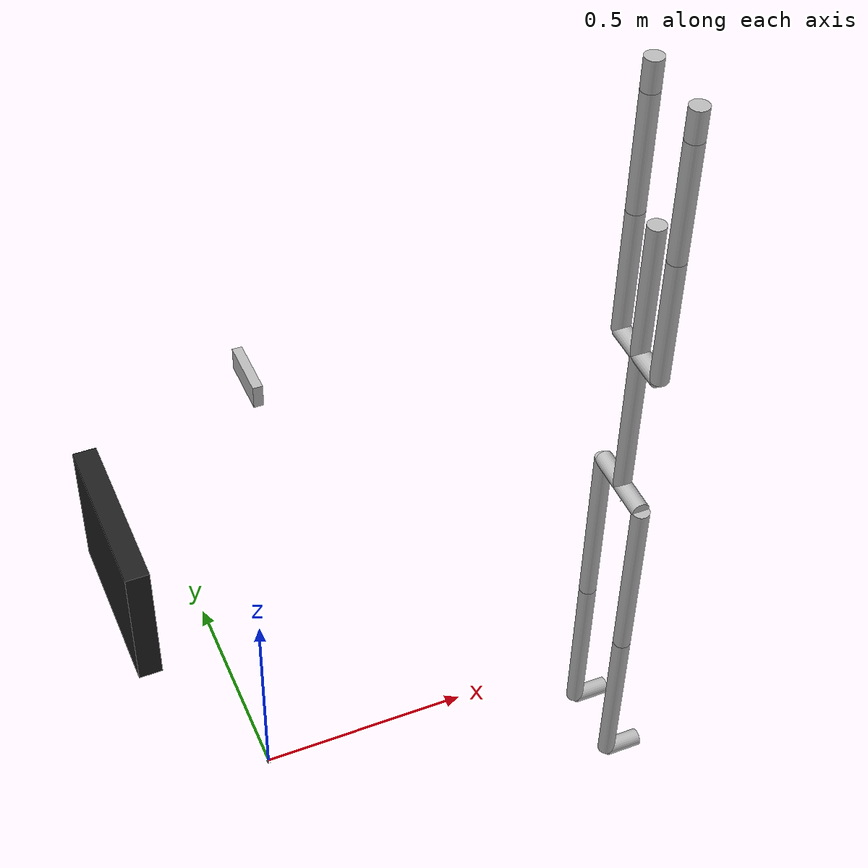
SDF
<sdf version="1.5">
  <model name="combined_human_pr2">
    <link name="base_footprint">
      <pose>0.0 0.0 0.0 0.0 -0.0 0.0</pose>
      <inertial>
        <pose>-0.0624209 0.0 0.201365 0.0 -0.0 0.0</pose>
        <mass>118.001</mass>
        <inertia>
          <ixx>6.13665</ixx>
          <ixy>-0.00971993</ixy>
          <ixz>1.455</ixz>
          <iyy>6.20983</iyy>
          <iyz>-0.00737958</iyz>
          <izz>3.75933</izz>
        </inertia>
      </inertial>
      <collision name="base_footprint_collision">
        <pose>0.0 0.0 0.071 0.0 -0.0 0.0</pose>
        <geometry>
          <box>
            <size>0.001 0.001 0.001</size>
          </box>
        </geometry>
      </collision>
      <collision name="base_footprint_collision_base_bellow_link">
        <pose>-0.29 0.0 0.851 0.0 -0.0 0.0</pose>
        <geometry>
          <box>
            <size>0.05 0.37 0.3</size>
          </box>
        </geometry>
        <surface>
          <contact>
            <ode/>
          </contact>
          <friction>
            <ode/>
          </friction>
        </surface>
      </collision>
      <!-- Moby lacks mesh support -->
      <visual name="base_footprint_visual">
        <pose>0.0 0.0 0.0 0.0 -0.0 0.0</pose>
        <geometry>
          <box>
            <size>0.01 0.01 0.01</size>
          </box>
        </geometry>
      </visual>
      <visual name="base_footprint_visual_base_bellow_link">
        <pose>-0.29 0.0 0.851 0.0 -0.0 0.0</pose>
        <geometry>
          <box>
            <size>0.05 0.37 0.3</size>
          </box>
        </geometry>
        <material>
          <script>
            <name>PR2/Black</name>
            <uri>__default__</uri>
          </script>
        </material>
      </visual>
      <!-- Moby lacks mesh support -->
      <velocity_decay>
        <linear>0.0</linear>
        <angular>0.0</angular>
      </velocity_decay>
      <sensor name="base_contact_sensor" type="contact">
        <always_on>1</always_on>
        <update_rate>100.0</update_rate>
        <contact>
          <collision>base_link_geom</collision>
          <topic>__default_topic__</topic>
        </contact>
        <pose>0.0 0.0 0.051 0.0 -0.0 0.0</pose>
      </sensor>
      <velocity_decay>
        <linear>0.0</linear>
        <angular>0.0</angular>
      </velocity_decay>
      <gravity>1</gravity>
      <velocity_decay>
        <linear>0.0</linear>
        <angular>0.0</angular>
      </velocity_decay>
      <self_collide>0.0</self_collide>
      <sensor name="base_laser" type="ray">
        <always_on>1</always_on>
        <update_rate>20.0</update_rate>
        <visualize>0.0</visualize>
        <ray>
          <scan>
            <horizontal>
              <samples>640.0</samples>
              <resolution>1</resolution>
              <min_angle>-2.2689</min_angle>
              <max_angle>2.2689</max_angle>
            </horizontal>
          </scan>
          <range>
            <min>0.08</min>
            <max>10.0</max>
            <resolution>0.01</resolution>
          </range>
        </ray>
        <pose>0.275 0.0 0.303 0.0 -0.0 0.0</pose>
      </sensor>
    </link>
    <link name="bl_caster_rotation_link">
      <pose>-0.2246 0.2246 0.0792 0.0 -0.0 0.0</pose>
      <inertial>
        <pose>0.0 0.0 0.07 0.0 -0.0 0.0</pose>
        <mass>3.47308</mass>
        <inertia>
          <ixx>0.0124118</ixx>
          <ixy>-0.000711734</ixy>
          <ixz>0.00050273</ixz>
          <iyy>0.0152182</iyy>
          <iyz>-4.27347e-06</iyz>
          <izz>0.011764</izz>
        </inertia>
      </inertial>
      <!-- Moby lacks mesh support -->
      <!-- Moby lacks mesh support -->
      <gravity>1</gravity>
      <velocity_decay>
        <linear>0.0</linear>
        <angular>0.0</angular>
      </velocity_decay>
      <self_collide>0.0</self_collide>
    </link>
    <joint name="bl_caster_rotation_joint" type="revolute">
      <child>bl_caster_rotation_link</child>
      <parent>base_footprint</parent>
      <axis>
        <xyz>0.0 0.0 1</xyz>
        <limit>
          <lower>-1e+16</lower>
          <upper>1e+16</upper>
        </limit>
        <dynamics>
          <damping>1</damping>
          <spring_reference>0.0</spring_reference>
          <spring_stiffness>0.0</spring_stiffness>
        </dynamics>
        <use_parent_model_frame>1</use_parent_model_frame>
      </axis>
    </joint>
    <link name="bl_caster_l_wheel_link">
      <pose>-0.2246 0.2736 0.0792 0.0 -0.0 0.0</pose>
      <inertial>
        <pose>0.0 0.0 0.0 0.0 -0.0 0.0</pose>
        <mass>0.44036</mass>
        <inertia>
          <ixx>0.0124118</ixx>
          <ixy>-0.000711734</ixy>
          <ixz>0.00050273</ixz>
          <iyy>0.0152182</iyy>
          <iyz>-4.27347e-06</iyz>
          <izz>0.011764</izz>
        </inertia>
      </inertial>
      <collision name="bl_caster_l_wheel_link_collision">
        <pose>0.0 0.0 0.0 1.5708 -0.0 0.0</pose>
        <geometry>
          <cylinder>
            <length>0.034</length>
            <radius>0.074792</radius>
          </cylinder>
        </geometry>
        <surface>
          <contact>
            <ode>
              <kp>1e+06</kp>
              <kd>1</kd>
              <max_vel>100.0</max_vel>
              <min_depth>0.0</min_depth>
            </ode>
          </contact>
          <friction>
            <ode>
              <mu>100.0</mu>
              <mu2>100.0</mu2>
            </ode>
          </friction>
        </surface>
      </collision>
      <!-- Moby lacks mesh support -->
      <gravity>1</gravity>
      <velocity_decay>
        <linear>0.0</linear>
        <angular>0.0</angular>
      </velocity_decay>
      <self_collide>0.0</self_collide>
    </link>
    <joint name="bl_caster_l_wheel_joint" type="revolute">
      <child>bl_caster_l_wheel_link</child>
      <parent>bl_caster_rotation_link</parent>
      <axis>
        <xyz>0.0 1 0.0</xyz>
        <limit>
          <lower>-1e+16</lower>
          <upper>1e+16</upper>
        </limit>
        <dynamics>
          <damping>1</damping>
          <spring_reference>0.0</spring_reference>
          <spring_stiffness>0.0</spring_stiffness>
        </dynamics>
        <use_parent_model_frame>1</use_parent_model_frame>
      </axis>
    </joint>
    <link name="bl_caster_r_wheel_link">
      <pose>-0.2246 0.1756 0.0792 0.0 -0.0 0.0</pose>
      <inertial>
        <pose>0.0 0.0 0.0 0.0 -0.0 0.0</pose>
        <mass>0.44036</mass>
        <inertia>
          <ixx>0.0124118</ixx>
          <ixy>-0.000711734</ixy>
          <ixz>0.00050273</ixz>
          <iyy>0.0152182</iyy>
          <iyz>-4.27347e-06</iyz>
          <izz>0.011764</izz>
        </inertia>
      </inertial>
      <collision name="bl_caster_r_wheel_link_collision">
        <pose>0.0 0.0 0.0 1.5708 -0.0 0.0</pose>
        <geometry>
          <cylinder>
            <length>0.034</length>
            <radius>0.074792</radius>
          </cylinder>
        </geometry>
        <surface>
          <contact>
            <ode>
              <kp>1e+06</kp>
              <kd>1</kd>
              <max_vel>100.0</max_vel>
              <min_depth>0.0</min_depth>
            </ode>
          </contact>
          <friction>
            <ode>
              <mu>100.0</mu>
              <mu2>100.0</mu2>
            </ode>
          </friction>
        </surface>
      </collision>
      <!-- Moby lacks mesh support -->
      <gravity>1</gravity>
      <velocity_decay>
        <linear>0.0</linear>
        <angular>0.0</angular>
      </velocity_decay>
      <self_collide>0.0</self_collide>
    </link>
    <joint name="bl_caster_r_wheel_joint" type="revolute">
      <child>bl_caster_r_wheel_link</child>
      <parent>bl_caster_rotation_link</parent>
      <axis>
        <xyz>0.0 1 0.0</xyz>
        <limit>
          <lower>-1e+16</lower>
          <upper>1e+16</upper>
        </limit>
        <dynamics>
          <damping>1</damping>
          <spring_reference>0.0</spring_reference>
          <spring_stiffness>0.0</spring_stiffness>
        </dynamics>
        <use_parent_model_frame>1</use_parent_model_frame>
      </axis>
    </joint>
    <link name="br_caster_rotation_link">
      <pose>-0.2246 -0.2246 0.0792 0.0 -0.0 0.0</pose>
      <inertial>
        <pose>0.0 0.0 0.07 0.0 -0.0 0.0</pose>
        <mass>3.47308</mass>
        <inertia>
          <ixx>0.0124118</ixx>
          <ixy>-0.000711734</ixy>
          <ixz>0.00050273</ixz>
          <iyy>0.0152182</iyy>
          <iyz>-4.27347e-06</iyz>
          <izz>0.011764</izz>
        </inertia>
      </inertial>
      <!-- Moby lacks mesh support -->
      <!-- Moby lacks mesh support -->
      <gravity>1</gravity>
      <velocity_decay>
        <linear>0.0</linear>
        <angular>0.0</angular>
      </velocity_decay>
      <self_collide>0.0</self_collide>
    </link>
    <joint name="br_caster_rotation_joint" type="revolute">
      <child>br_caster_rotation_link</child>
      <parent>base_footprint</parent>
      <axis>
        <xyz>0.0 0.0 1</xyz>
        <limit>
          <lower>-1e+16</lower>
          <upper>1e+16</upper>
        </limit>
        <dynamics>
          <damping>1</damping>
          <spring_reference>0.0</spring_reference>
          <spring_stiffness>0.0</spring_stiffness>
        </dynamics>
        <use_parent_model_frame>1</use_parent_model_frame>
      </axis>
    </joint>
    <link name="br_caster_l_wheel_link">
      <pose>-0.2246 -0.1756 0.0792 0.0 -0.0 0.0</pose>
      <inertial>
        <pose>0.0 0.0 0.0 0.0 -0.0 0.0</pose>
        <mass>0.44036</mass>
        <inertia>
          <ixx>0.0124118</ixx>
          <ixy>-0.000711734</ixy>
          <ixz>0.00050273</ixz>
          <iyy>0.0152182</iyy>
          <iyz>-4.27347e-06</iyz>
          <izz>0.011764</izz>
        </inertia>
      </inertial>
      <collision name="br_caster_l_wheel_link_collision">
        <pose>0.0 0.0 0.0 1.5708 -0.0 0.0</pose>
        <geometry>
          <cylinder>
            <length>0.034</length>
            <radius>0.074792</radius>
          </cylinder>
        </geometry>
        <surface>
          <contact>
            <ode>
              <kp>1e+06</kp>
              <kd>1</kd>
              <max_vel>100.0</max_vel>
              <min_depth>0.0</min_depth>
            </ode>
          </contact>
          <friction>
            <ode>
              <mu>100.0</mu>
              <mu2>100.0</mu2>
            </ode>
          </friction>
        </surface>
      </collision>
      <!-- Moby lacks mesh support -->
      <gravity>1</gravity>
      <velocity_decay>
        <linear>0.0</linear>
        <angular>0.0</angular>
      </velocity_decay>
      <self_collide>0.0</self_collide>
    </link>
    <joint name="br_caster_l_wheel_joint" type="revolute">
      <child>br_caster_l_wheel_link</child>
      <parent>br_caster_rotation_link</parent>
      <axis>
        <xyz>0.0 1 0.0</xyz>
        <limit>
          <lower>-1e+16</lower>
          <upper>1e+16</upper>
        </limit>
        <dynamics>
          <damping>1</damping>
          <spring_reference>0.0</spring_reference>
          <spring_stiffness>0.0</spring_stiffness>
        </dynamics>
        <use_parent_model_frame>1</use_parent_model_frame>
      </axis>
    </joint>
    <link name="br_caster_r_wheel_link">
      <pose>-0.2246 -0.2736 0.0792 0.0 -0.0 0.0</pose>
      <inertial>
        <pose>0.0 0.0 0.0 0.0 -0.0 0.0</pose>
        <mass>0.44036</mass>
        <inertia>
          <ixx>0.0124118</ixx>
          <ixy>-0.000711734</ixy>
          <ixz>0.00050273</ixz>
          <iyy>0.0152182</iyy>
          <iyz>-4.27347e-06</iyz>
          <izz>0.011764</izz>
        </inertia>
      </inertial>
      <collision name="br_caster_r_wheel_link_collision">
        <pose>0.0 0.0 0.0 1.5708 -0.0 0.0</pose>
        <geometry>
          <cylinder>
            <length>0.034</length>
            <radius>0.074792</radius>
          </cylinder>
        </geometry>
        <surface>
          <contact>
            <ode>
              <kp>1e+06</kp>
              <kd>1</kd>
              <max_vel>100.0</max_vel>
              <min_depth>0.0</min_depth>
            </ode>
          </contact>
          <friction>
            <ode>
              <mu>100.0</mu>
              <mu2>100.0</mu2>
            </ode>
          </friction>
        </surface>
      </collision>
      <!-- Moby lacks mesh support -->
      <gravity>1</gravity>
      <velocity_decay>
        <linear>0.0</linear>
        <angular>0.0</angular>
      </velocity_decay>
      <self_collide>0.0</self_collide>
    </link>
    <joint name="br_caster_r_wheel_joint" type="revolute">
      <child>br_caster_r_wheel_link</child>
      <parent>br_caster_rotation_link</parent>
      <axis>
        <xyz>0.0 1 0.0</xyz>
        <limit>
          <lower>-1e+16</lower>
          <upper>1e+16</upper>
        </limit>
        <dynamics>
          <damping>1</damping>
          <spring_reference>0.0</spring_reference>
          <spring_stiffness>0.0</spring_stiffness>
        </dynamics>
        <use_parent_model_frame>1</use_parent_model_frame>
      </axis>
    </joint>
    <link name="fl_caster_rotation_link">
      <pose>0.2246 0.2246 0.0792 0.0 -0.0 0.0</pose>
      <inertial>
        <pose>0.0 0.0 0.07 0.0 -0.0 0.0</pose>
        <mass>3.47308</mass>
        <inertia>
          <ixx>0.0124118</ixx>
          <ixy>-0.000711734</ixy>
          <ixz>0.00050273</ixz>
          <iyy>0.0152182</iyy>
          <iyz>-4.27347e-06</iyz>
          <izz>0.011764</izz>
        </inertia>
      </inertial>
      <!-- Moby lacks mesh support -->
      <!-- Moby lacks mesh support -->
      <gravity>1</gravity>
      <velocity_decay>
        <linear>0.0</linear>
        <angular>0.0</angular>
      </velocity_decay>
      <self_collide>0.0</self_collide>
    </link>
    <joint name="fl_caster_rotation_joint" type="revolute">
      <child>fl_caster_rotation_link</child>
      <parent>base_footprint</parent>
      <axis>
        <xyz>0.0 0.0 1</xyz>
        <limit>
          <lower>-1e+16</lower>
          <upper>1e+16</upper>
        </limit>
        <dynamics>
          <damping>1</damping>
          <spring_reference>0.0</spring_reference>
          <spring_stiffness>0.0</spring_stiffness>
        </dynamics>
        <use_parent_model_frame>1</use_parent_model_frame>
      </axis>
    </joint>
    <link name="fl_caster_l_wheel_link">
      <pose>0.2246 0.2736 0.0792 0.0 -0.0 0.0</pose>
      <inertial>
        <pose>0.0 0.0 0.0 0.0 -0.0 0.0</pose>
        <mass>0.44036</mass>
        <inertia>
          <ixx>0.0124118</ixx>
          <ixy>-0.000711734</ixy>
          <ixz>0.00050273</ixz>
          <iyy>0.0152182</iyy>
          <iyz>-4.27347e-06</iyz>
          <izz>0.011764</izz>
        </inertia>
      </inertial>
      <collision name="fl_caster_l_wheel_link_collision">
        <pose>0.0 0.0 0.0 1.5708 -0.0 0.0</pose>
        <geometry>
          <cylinder>
            <length>0.034</length>
            <radius>0.074792</radius>
          </cylinder>
        </geometry>
        <surface>
          <contact>
            <ode>
              <kp>1e+06</kp>
              <kd>1</kd>
              <max_vel>100.0</max_vel>
              <min_depth>0.0</min_depth>
            </ode>
          </contact>
          <friction>
            <ode>
              <mu>100.0</mu>
              <mu2>100.0</mu2>
            </ode>
          </friction>
        </surface>
      </collision>
      <!-- Moby lacks mesh support -->
      <gravity>1</gravity>
      <velocity_decay>
        <linear>0.0</linear>
        <angular>0.0</angular>
      </velocity_decay>
      <self_collide>0.0</self_collide>
    </link>
    <joint name="fl_caster_l_wheel_joint" type="revolute">
      <child>fl_caster_l_wheel_link</child>
      <parent>fl_caster_rotation_link</parent>
      <axis>
        <xyz>0.0 1 0.0</xyz>
        <limit>
          <lower>-1e+16</lower>
          <upper>1e+16</upper>
        </limit>
        <dynamics>
          <damping>1</damping>
          <spring_reference>0.0</spring_reference>
          <spring_stiffness>0.0</spring_stiffness>
        </dynamics>
        <use_parent_model_frame>1</use_parent_model_frame>
      </axis>
    </joint>
    <link name="fl_caster_r_wheel_link">
      <pose>0.2246 0.1756 0.0792 0.0 -0.0 0.0</pose>
      <inertial>
        <pose>0.0 0.0 0.0 0.0 -0.0 0.0</pose>
        <mass>0.44036</mass>
        <inertia>
          <ixx>0.0124118</ixx>
          <ixy>-0.000711734</ixy>
          <ixz>0.00050273</ixz>
          <iyy>0.0152182</iyy>
          <iyz>-4.27347e-06</iyz>
          <izz>0.011764</izz>
        </inertia>
      </inertial>
      <collision name="fl_caster_r_wheel_link_collision">
        <pose>0.0 0.0 0.0 1.5708 -0.0 0.0</pose>
        <geometry>
          <cylinder>
            <length>0.034</length>
            <radius>0.074792</radius>
          </cylinder>
        </geometry>
        <surface>
          <contact>
            <ode>
              <kp>1e+06</kp>
              <kd>1</kd>
              <max_vel>100.0</max_vel>
              <min_depth>0.0</min_depth>
            </ode>
          </contact>
          <friction>
            <ode>
              <mu>100.0</mu>
              <mu2>100.0</mu2>
            </ode>
          </friction>
        </surface>
      </collision>
      <!-- Moby lacks mesh support -->
      <gravity>1</gravity>
      <velocity_decay>
        <linear>0.0</linear>
        <angular>0.0</angular>
      </velocity_decay>
      <self_collide>0.0</self_collide>
    </link>
    <joint name="fl_caster_r_wheel_joint" type="revolute">
      <child>fl_caster_r_wheel_link</child>
      <parent>fl_caster_rotation_link</parent>
      <axis>
        <xyz>0.0 1 0.0</xyz>
        <limit>
          <lower>-1e+16</lower>
          <upper>1e+16</upper>
        </limit>
        <dynamics>
          <damping>1</damping>
          <spring_reference>0.0</spring_reference>
          <spring_stiffness>0.0</spring_stiffness>
        </dynamics>
        <use_parent_model_frame>1</use_parent_model_frame>
      </axis>
    </joint>
    <link name="fr_caster_rotation_link">
      <pose>0.2246 -0.2246 0.0792 0.0 -0.0 0.0</pose>
      <inertial>
        <pose>0.0 0.0 0.07 0.0 -0.0 0.0</pose>
        <mass>3.47308</mass>
        <inertia>
          <ixx>0.0124118</ixx>
          <ixy>-0.000711734</ixy>
          <ixz>0.00050273</ixz>
          <iyy>0.0152182</iyy>
          <iyz>-4.27347e-06</iyz>
          <izz>0.011764</izz>
        </inertia>
      </inertial>
      <!-- Moby lacks mesh support -->
      <!-- Moby lacks mesh support -->
      <gravity>1</gravity>
      <velocity_decay>
        <linear>0.0</linear>
        <angular>0.0</angular>
      </velocity_decay>
      <self_collide>0.0</self_collide>
    </link>
    <joint name="fr_caster_rotation_joint" type="revolute">
      <child>fr_caster_rotation_link</child>
      <parent>base_footprint</parent>
      <axis>
        <xyz>0.0 0.0 1</xyz>
        <limit>
          <lower>-1e+16</lower>
          <upper>1e+16</upper>
        </limit>
        <dynamics>
          <damping>1</damping>
          <spring_reference>0.0</spring_reference>
          <spring_stiffness>0.0</spring_stiffness>
        </dynamics>
        <use_parent_model_frame>1</use_parent_model_frame>
      </axis>
    </joint>
    <link name="fr_caster_l_wheel_link">
      <pose>0.2246 -0.1756 0.0792 0.0 -0.0 0.0</pose>
      <inertial>
        <pose>0.0 0.0 0.0 0.0 -0.0 0.0</pose>
        <mass>0.44036</mass>
        <inertia>
          <ixx>0.0124118</ixx>
          <ixy>-0.000711734</ixy>
          <ixz>0.00050273</ixz>
          <iyy>0.0152182</iyy>
          <iyz>-4.27347e-06</iyz>
          <izz>0.011764</izz>
        </inertia>
      </inertial>
      <collision name="fr_caster_l_wheel_link_collision">
        <pose>0.0 0.0 0.0 1.5708 -0.0 0.0</pose>
        <geometry>
          <cylinder>
            <length>0.034</length>
            <radius>0.074792</radius>
          </cylinder>
        </geometry>
        <surface>
          <contact>
            <ode>
              <kp>1e+06</kp>
              <kd>1</kd>
              <max_vel>100.0</max_vel>
              <min_depth>0.0</min_depth>
            </ode>
          </contact>
          <friction>
            <ode>
              <mu>100.0</mu>
              <mu2>100.0</mu2>
            </ode>
          </friction>
        </surface>
      </collision>
      <!-- Moby lacks mesh support -->
      <gravity>1</gravity>
      <velocity_decay>
        <linear>0.0</linear>
        <angular>0.0</angular>
      </velocity_decay>
      <self_collide>0.0</self_collide>
    </link>
    <joint name="fr_caster_l_wheel_joint" type="revolute">
      <child>fr_caster_l_wheel_link</child>
      <parent>fr_caster_rotation_link</parent>
      <axis>
        <xyz>0.0 1 0.0</xyz>
        <limit>
          <lower>-1e+16</lower>
          <upper>1e+16</upper>
        </limit>
        <dynamics>
          <damping>1</damping>
          <spring_reference>0.0</spring_reference>
          <spring_stiffness>0.0</spring_stiffness>
        </dynamics>
        <use_parent_model_frame>1</use_parent_model_frame>
      </axis>
    </joint>
    <link name="fr_caster_r_wheel_link">
      <pose>0.2246 -0.2736 0.0792 0.0 -0.0 0.0</pose>
      <inertial>
        <pose>0.0 0.0 0.0 0.0 -0.0 0.0</pose>
        <mass>0.44036</mass>
        <inertia>
          <ixx>0.0124118</ixx>
          <ixy>-0.000711734</ixy>
          <ixz>0.00050273</ixz>
          <iyy>0.0152182</iyy>
          <iyz>-4.27347e-06</iyz>
          <izz>0.011764</izz>
        </inertia>
      </inertial>
      <collision name="fr_caster_r_wheel_link_collision">
        <pose>0.0 0.0 0.0 1.5708 -0.0 0.0</pose>
        <geometry>
          <cylinder>
            <length>0.034</length>
            <radius>0.074792</radius>
          </cylinder>
        </geometry>
        <surface>
          <contact>
            <ode>
              <kp>1e+06</kp>
              <kd>1</kd>
              <max_vel>100.0</max_vel>
              <min_depth>0.0</min_depth>
            </ode>
          </contact>
          <friction>
            <ode>
              <mu>100.0</mu>
              <mu2>100.0</mu2>
            </ode>
          </friction>
        </surface>
      </collision>
      <!-- Moby lacks mesh support -->
      <gravity>1</gravity>
      <velocity_decay>
        <linear>0.0</linear>
        <angular>0.0</angular>
      </velocity_decay>
      <self_collide>0.0</self_collide>
    </link>
    <joint name="fr_caster_r_wheel_joint" type="revolute">
      <child>fr_caster_r_wheel_link</child>
      <parent>fr_caster_rotation_link</parent>
      <axis>
        <xyz>0.0 1 0.0</xyz>
        <limit>
          <lower>-1e+16</lower>
          <upper>1e+16</upper>
        </limit>
        <dynamics>
          <damping>1</damping>
          <spring_reference>0.0</spring_reference>
          <spring_stiffness>0.0</spring_stiffness>
        </dynamics>
        <use_parent_model_frame>1</use_parent_model_frame>
      </axis>
    </joint>
    <link name="torso_lift_link">
      <pose>-0.05 0.0 0.790675 0.0 -0.0 0.0</pose>
      <inertial>
        <pose>-0.0994987 -4.1071e-06 -0.0867639 0.0 -0.0 0.0</pose>
        <mass>36.449</mass>
        <inertia>
          <ixx>2.80235</ixx>
          <ixy>0.00429496</ixy>
          <ixz>-0.16614</ixz>
          <iyy>2.53349</iyy>
          <iyz>0.029702</iyz>
          <izz>0.538967</izz>
        </inertia>
      </inertial>
      <!-- Moby lacks mesh support -->
      <!-- Moby lacks mesh support -->
      <gravity>1</gravity>
      <velocity_decay>
        <linear>0.0</linear>
        <angular>0.0</angular>
      </velocity_decay>
      <self_collide>0.0</self_collide>
      <sensor name="torso_lift_contact_sensor" type="contact">
        <contact>
          <collision>torso_lift_link_geom</collision>
          <topic>__default_topic__</topic>
        </contact>
        <update_rate>100.0</update_rate>
      </sensor>
    </link>
    <joint name="torso_lift_joint" type="prismatic">
      <child>torso_lift_link</child>
      <parent>base_footprint</parent>
      <axis>
        <xyz>0.0 0.0 1</xyz>
        <limit>
          <lower>0.0</lower>
          <upper>0.33</upper>
          <effort>10000.0</effort>
          <velocity>0.013</velocity>
        </limit>
        <dynamics>
          <damping>20000.0</damping>
          <spring_reference>0.0</spring_reference>
          <spring_stiffness>0.0</spring_stiffness>
        </dynamics>
        <use_parent_model_frame>1</use_parent_model_frame>
      </axis>
    </joint>
    <link name="head_pan_link">
      <pose>-0.06707 0.0 1.17213 0.0 -0.0 0.0</pose>
      <inertial>
        <pose>0.010907 0.031693 0.090507 0.0 -0.0 0.0</pose>
        <mass>6.339</mass>
        <inertia>
          <ixx>0.0324976</ixx>
          <ixy>0.000636041</ixy>
          <ixz>0.00258515</ixz>
          <iyy>0.0465456</iyy>
          <iyz>-0.00245343</iyz>
          <izz>0.0576527</izz>
        </inertia>
      </inertial>
      <!-- Moby lacks mesh support -->
      <velocity_decay>
        <linear>0.0</linear>
        <angular>0.0</angular>
      </velocity_decay>
    </link>
    <joint name="head_pan_joint" type="revolute">
      <child>head_pan_link</child>
      <parent>torso_lift_link</parent>
      <axis>
        <xyz>0.0 0.0 1</xyz>
        <limit>
          <lower>-3.007</lower>
          <upper>3.007</upper>
          <effort>2.645</effort>
          <velocity>6</velocity>
        </limit>
        <dynamics>
          <damping>0.5</damping>
          <spring_reference>0.0</spring_reference>
          <spring_stiffness>0.0</spring_stiffness>
        </dynamics>
        <use_parent_model_frame>1</use_parent_model_frame>
      </axis>
    </joint>
    <link name="head_tilt_link">
      <pose>0.00093 0.0 1.17213 0.0 -0.0 0.0</pose>
      <inertial>
        <pose>0.00621107 -0.0159771 0.05874 0.0 -0.0 0.0</pose>
        <mass>4.919</mass>
        <inertia>
          <ixx>0.057667</ixx>
          <ixy>-0.000330994</ixy>
          <ixz>-0.00117206</ixz>
          <iyy>0.0879055</iyy>
          <iyz>0.00196687</iyz>
          <izz>0.119008</izz>
        </inertia>
      </inertial>
      <!-- Moby lacks mesh support -->
      <collision name="head_tilt_link_collision_head_plate_frame">
        <pose>0.0232 0.0 0.0645 0.0 -0.0 0.0</pose>
        <geometry>
          <box>
            <size>0.01 0.01 0.01</size>
          </box>
        </geometry>
        <surface>
          <contact>
            <ode/>
          </contact>
          <friction>
            <ode/>
          </friction>
        </surface>
      </collision>
      <!-- Moby lacks mesh support -->
      <visual name="head_tilt_link_visual_double_stereo_link">
        <pose>0.0132 0.0 0.0895 0.0 -0.0 0.0</pose>
        <geometry>
          <box>
            <size>0.02 0.12 0.05</size>
          </box>
        </geometry>
      </visual>
      <visual name="head_tilt_link_visual_head_plate_frame">
        <pose>0.0232 0.0 0.0645 0.0 -0.0 0.0</pose>
        <geometry>
          <box>
            <size>0.01 0.01 0.01</size>
          </box>
        </geometry>
        <material>
          <script>
            <name>Gazebo/Grey</name>
            <uri>__default__</uri>
          </script>
        </material>
      </visual>
      <visual name="head_tilt_link_visual_sensor_mount_link">
        <pose>0.0232 0.0 0.0645 0.0 -0.0 0.0</pose>
        <geometry>
          <box>
            <size>0.01 0.01 0.01</size>
          </box>
        </geometry>
      </visual>
      <velocity_decay>
        <linear>0.0</linear>
        <angular>0.0</angular>
      </velocity_decay>
      <velocity_decay>
        <linear>0.0</linear>
        <angular>0.0</angular>
      </velocity_decay>
      <projector name="projector_wg6802418_projector_wg6802418">
        <texture>stereo_projection_pattern_high_res_red.png</texture>
        <fov>0.959931</fov>
        <near_clip>0.1</near_clip>
        <far_clip>10.0</far_clip>
        <pose>0.069657 0.11 0.1191 3.14159 -1.57079 3.14159</pose>
      </projector>
      <velocity_decay>
        <linear>0.0</linear>
        <angular>0.0</angular>
      </velocity_decay>
      <velocity_decay>
        <linear>0.0</linear>
        <angular>0.0</angular>
      </velocity_decay>
      <sensor name="narrow_stereo_l_stereo_camera_sensor" type="camera">
        <always_on>1</always_on>
        <update_rate>25</update_rate>
        <camera name="__default__">
          <horizontal_fov>0.785398</horizontal_fov>
          <image>
            <format>L8</format>
            <width>640.0</width>
            <height>480.0</height>
          </image>
          <clip>
            <near>0.1</near>
            <far>100.0</far>
          </clip>
        </camera>
        <pose>0.0682 0.06 0.1146 0.0 -0.0 0.0</pose>
      </sensor>
      <velocity_decay>
        <linear>0.0</linear>
        <angular>0.0</angular>
      </velocity_decay>
      <sensor name="narrow_stereo_r_stereo_camera_sensor" type="camera">
        <always_on>1</always_on>
        <update_rate>25</update_rate>
        <camera name="__default__">
          <horizontal_fov>0.785398</horizontal_fov>
          <image>
            <format>L8</format>
            <width>640.0</width>
            <height>480.0</height>
          </image>
          <clip>
            <near>0.1</near>
            <far>100.0</far>
          </clip>
        </camera>
        <pose>0.0682 -0.03 0.1146 0.0 -0.0 0.0</pose>
      </sensor>
      <velocity_decay>
        <linear>0.0</linear>
        <angular>0.0</angular>
      </velocity_decay>
      <velocity_decay>
        <linear>0.0</linear>
        <angular>0.0</angular>
      </velocity_decay>
      <velocity_decay>
        <linear>0.0</linear>
        <angular>0.0</angular>
      </velocity_decay>
      <sensor name="wide_stereo_l_stereo_camera_sensor" type="camera">
        <always_on>1</always_on>
        <update_rate>25</update_rate>
        <camera name="__default__">
          <horizontal_fov>1.5708</horizontal_fov>
          <image>
            <format>BAYER_BGGR8</format>
            <width>640.0</width>
            <height>480.0</height>
          </image>
          <clip>
            <near>0.1</near>
            <far>100.0</far>
          </clip>
        </camera>
        <pose>0.0682 0.03 0.1146 0.0 -0.0 0.0</pose>
      </sensor>
      <velocity_decay>
        <linear>0.0</linear>
        <angular>0.0</angular>
      </velocity_decay>
      <sensor name="wide_stereo_r_stereo_camera_sensor" type="camera">
        <always_on>1</always_on>
        <update_rate>25</update_rate>
        <camera name="__default__">
          <horizontal_fov>1.5708</horizontal_fov>
          <image>
            <format>BAYER_BGGR8</format>
            <width>640.0</width>
            <height>480.0</height>
          </image>
          <clip>
            <near>0.1</near>
            <far>100.0</far>
          </clip>
        </camera>
        <pose>0.0682 -0.06 0.1146 0.0 -0.0 0.0</pose>
      </sensor>
      <velocity_decay>
        <linear>0.0</linear>
        <angular>0.0</angular>
      </velocity_decay>
      <gravity>1</gravity>
      <velocity_decay>
        <linear>0.0</linear>
        <angular>0.0</angular>
      </velocity_decay>
      <self_collide>0.0</self_collide>
      <sensor name="high_def_sensor" type="camera">
        <always_on>1</always_on>
        <update_rate>20.0</update_rate>
        <camera name="__default__">
          <horizontal_fov>0.785398</horizontal_fov>
          <image>
            <format>R8G8B8</format>
            <width>2448</width>
            <height>2050.0</height>
          </image>
          <clip>
            <near>0.1</near>
            <far>100.0</far>
          </clip>
        </camera>
        <pose>0.069657 -0.11 0.1191 0.0 -0.0 0.0</pose>
      </sensor>
    </link>
    <joint name="head_tilt_joint" type="revolute">
      <child>head_tilt_link</child>
      <parent>head_pan_link</parent>
      <axis>
        <xyz>0.0 1 0.0</xyz>
        <limit>
          <lower>-0.471238</lower>
          <upper>1.39626</upper>
          <effort>18</effort>
          <velocity>5</velocity>
        </limit>
        <dynamics>
          <damping>10.0</damping>
          <spring_reference>0.0</spring_reference>
          <spring_stiffness>0.0</spring_stiffness>
        </dynamics>
        <use_parent_model_frame>1</use_parent_model_frame>
      </axis>
    </joint>
    <link name="l_shoulder_pan_link">
      <pose>-0.05 0.188 0.790675 0.0 -0.0 0.0</pose>
      <inertial>
        <pose>-0.001201 0.024513 -0.098231 0.0 -0.0 0.0</pose>
        <mass>25.7993</mass>
        <inertia>
          <ixx>0.866179</ixx>
          <ixy>-0.0608651</ixy>
          <ixz>-0.121181</ixz>
          <iyy>0.874217</iyy>
          <iyz>-0.0588661</iyz>
          <izz>0.273538</izz>
        </inertia>
      </inertial>
      <!-- Moby lacks mesh support -->
      <!-- Moby lacks mesh support -->
      <gravity>0.0</gravity>
      <velocity_decay>
        <linear>0.0</linear>
        <angular>0.0</angular>
      </velocity_decay>
      <self_collide>0.0</self_collide>
    </link>
    <joint name="l_shoulder_pan_joint" type="revolute">
      <child>l_shoulder_pan_link</child>
      <parent>torso_lift_link</parent>
      <axis>
        <xyz>0.0 0.0 1</xyz>
        <limit>
          <lower>-0.714602</lower>
          <upper>2.2854</upper>
          <effort>30.0</effort>
          <velocity>2.088</velocity>
        </limit>
        <dynamics>
          <damping>10.0</damping>
          <spring_reference>0.0</spring_reference>
          <spring_stiffness>0.0</spring_stiffness>
        </dynamics>
        <use_parent_model_frame>1</use_parent_model_frame>
      </axis>
      <physics>
        <ode>
          <limit>
            <cfm>0.0</cfm>
            <erp>0.2</erp>
          </limit>
        </ode>
      </physics>
    </joint>
    <link name="l_shoulder_lift_link">
      <pose>0.05 0.188 0.790675 0.0 -0.0 0.0</pose>
      <inertial>
        <pose>0.02195 -0.02664 -0.03127 0.0 -0.0 0.0</pose>
        <mass>2.74988</mass>
        <inertia>
          <ixx>0.0210558</ixx>
          <ixy>0.00496704</ixy>
          <ixz>-0.00194809</ixz>
          <iyy>0.0212722</iyy>
          <iyz>0.00110425</iyz>
          <izz>0.0197575</izz>
        </inertia>
      </inertial>
      <!-- Moby lacks mesh support -->
      <!-- Moby lacks mesh support -->
      <gravity>0.0</gravity>
      <velocity_decay>
        <linear>0.0</linear>
        <angular>0.0</angular>
      </velocity_decay>
      <self_collide>0.0</self_collide>
    </link>
    <joint name="l_shoulder_lift_joint" type="revolute">
      <child>l_shoulder_lift_link</child>
      <parent>l_shoulder_pan_link</parent>
      <axis>
        <xyz>0.0 1 0.0</xyz>
        <limit>
          <lower>-0.5236</lower>
          <upper>1.3963</upper>
          <effort>30.0</effort>
          <velocity>2.082</velocity>
        </limit>
        <dynamics>
          <damping>10.0</damping>
          <spring_reference>0.0</spring_reference>
          <spring_stiffness>0.0</spring_stiffness>
        </dynamics>
        <use_parent_model_frame>1</use_parent_model_frame>
      </axis>
      <physics>
        <ode>
          <limit>
            <cfm>0.0</cfm>
            <erp>0.2</erp>
          </limit>
        </ode>
      </physics>
    </joint>
    <link name="l_upper_arm_roll_link">
      <pose>0.05 0.188 0.790675 0.0 -0.0 0.0</pose>
      <inertial>
        <pose>0.210551 0.016309 -0.000560683 0.0 -0.0 0.0</pose>
        <mass>6.11769</mass>
        <inertia>
          <ixx>0.0253331</ixx>
          <ixy>-0.00374234</ixy>
          <ixz>0.000619656</ixz>
          <iyy>0.0892438</iyy>
          <iyz>-0.000198608</iyz>
          <izz>0.0905498</izz>
        </inertia>
      </inertial>
      <!-- Moby lacks mesh support -->
      <!-- Moby lacks mesh support -->
      <!-- Moby lacks mesh support -->
      <velocity_decay>
        <linear>0.0</linear>
        <angular>0.0</angular>
      </velocity_decay>
      <gravity>0.0</gravity>
      <velocity_decay>
        <linear>0.0</linear>
        <angular>0.0</angular>
      </velocity_decay>
      <self_collide>0.0</self_collide>
    </link>
    <joint name="l_upper_arm_roll_joint" type="revolute">
      <child>l_upper_arm_roll_link</child>
      <parent>l_shoulder_lift_link</parent>
      <axis>
        <xyz>1 0.0 0.0</xyz>
        <limit>
          <lower>-0.8</lower>
          <upper>3.9</upper>
          <effort>30.0</effort>
          <velocity>3.27</velocity>
        </limit>
        <dynamics>
          <damping>0.1</damping>
          <spring_reference>0.0</spring_reference>
          <spring_stiffness>0.0</spring_stiffness>
        </dynamics>
        <use_parent_model_frame>1</use_parent_model_frame>
      </axis>
      <physics>
        <ode>
          <fudge_factor>0.5</fudge_factor>
          <limit>
            <cfm>0.0</cfm>
            <erp>0.2</erp>
          </limit>
        </ode>
      </physics>
    </joint>
    <link name="l_elbow_flex_link">
      <pose>0.45 0.188 0.790675 0.0 -0.0 0.0</pose>
      <inertial>
        <pose>0.01014 0.00032 -0.01211 0.0 -0.0 0.0</pose>
        <mass>1.90327</mass>
        <inertia>
          <ixx>0.00346542</ixx>
          <ixy>4.06683e-05</ixy>
          <ixz>0.000431716</ixz>
          <iyy>0.00441606</iyy>
          <iyz>-3.96891e-05</iyz>
          <izz>0.00359157</izz>
        </inertia>
      </inertial>
      <!-- Moby lacks mesh support -->
      <!-- Moby lacks mesh support -->
      <gravity>0.0</gravity>
      <velocity_decay>
        <linear>0.0</linear>
        <angular>0.0</angular>
      </velocity_decay>
      <self_collide>0.0</self_collide>
    </link>
    <joint name="l_elbow_flex_joint" type="revolute">
      <child>l_elbow_flex_link</child>
      <parent>l_upper_arm_roll_link</parent>
      <axis>
        <xyz>0.0 1 0.0</xyz>
        <limit>
          <lower>-2.3213</lower>
          <upper>0.0</upper>
          <effort>30.0</effort>
          <velocity>3.3</velocity>
        </limit>
        <dynamics>
          <damping>1</damping>
          <spring_reference>0.0</spring_reference>
          <spring_stiffness>0.0</spring_stiffness>
        </dynamics>
        <use_parent_model_frame>1</use_parent_model_frame>
      </axis>
      <physics>
        <ode>
          <limit>
            <cfm>0.0</cfm>
            <erp>0.2</erp>
          </limit>
        </ode>
      </physics>
    </joint>
    <link name="l_forearm_roll_link">
      <pose>0.45 0.188 0.790675 0.0 -0.0 0.0</pose>
      <inertial>
        <pose>0.180727 -0.000163048 -0.00858343 0.0 -0.0 0.0</pose>
        <mass>2.68968</mass>
        <inertia>
          <ixx>0.0146843</ixx>
          <ixy>5.53089e-05</ixy>
          <ixz>0.000904462</ixz>
          <iyy>0.0295334</iyy>
          <iyz>-1.3343e-05</iyz>
          <izz>0.0310133</izz>
        </inertia>
      </inertial>
      <!-- Moby lacks mesh support -->
      <!-- Moby lacks mesh support -->
      <!-- Moby lacks mesh support -->
      <!-- Moby lacks mesh support -->
      <velocity_decay>
        <linear>0.0</linear>
        <angular>0.0</angular>
      </velocity_decay>
      <velocity_decay>
        <linear>0.0</linear>
        <angular>0.0</angular>
      </velocity_decay>
      <sensor name="l_forearm_cam_sensor" type="camera">
        <always_on>1</always_on>
        <update_rate>25</update_rate>
        <camera name="__default__">
          <horizontal_fov>1.5708</horizontal_fov>
          <image>
            <format>R8G8B8</format>
            <width>640.0</width>
            <height>480.0</height>
          </image>
          <clip>
            <near>0.1</near>
            <far>100.0</far>
          </clip>
        </camera>
        <pose>0.135 0.0 0.044 -1.5708 -0.562869 0.0</pose>
      </sensor>
      <gravity>0.0</gravity>
      <velocity_decay>
        <linear>0.0</linear>
        <angular>0.0</angular>
      </velocity_decay>
      <self_collide>0.0</self_collide>
    </link>
    <joint name="l_forearm_roll_joint" type="revolute">
      <child>l_forearm_roll_link</child>
      <parent>l_elbow_flex_link</parent>
      <axis>
        <xyz>1 0.0 0.0</xyz>
        <limit>
          <lower>-1e+16</lower>
          <upper>1e+16</upper>
        </limit>
        <dynamics>
          <damping>0.1</damping>
          <spring_reference>0.0</spring_reference>
          <spring_stiffness>0.0</spring_stiffness>
        </dynamics>
        <use_parent_model_frame>1</use_parent_model_frame>
      </axis>
      <physics>
        <ode>
          <fudge_factor>0.5</fudge_factor>
          <limit>
            <cfm>0.0</cfm>
            <erp>0.2</erp>
          </limit>
        </ode>
      </physics>
    </joint>
    <link name="l_wrist_flex_link">
      <pose>0.771 0.188 0.790675 0.0 -0.0 0.0</pose>
      <inertial>
        <pose>-0.00157 0.0 -0.00075 0.0 -0.0 0.0</pose>
        <mass>0.61402</mass>
        <inertia>
          <ixx>0.000651657</ixx>
          <ixy>2.8864e-07</ixy>
          <ixz>3.03477e-06</ixz>
          <iyy>0.000198244</iyy>
          <iyz>-2.2645e-07</iyz>
          <izz>0.000644505</izz>
        </inertia>
      </inertial>
      <!-- Moby lacks mesh support -->
      <!-- Moby lacks mesh support -->
      <gravity>0.0</gravity>
      <velocity_decay>
        <linear>0.0</linear>
        <angular>0.0</angular>
      </velocity_decay>
      <self_collide>0.0</self_collide>
    </link>
    <joint name="l_wrist_flex_joint" type="revolute">
      <child>l_wrist_flex_link</child>
      <parent>l_forearm_roll_link</parent>
      <axis>
        <xyz>0.0 1 0.0</xyz>
        <limit>
          <lower>-2.18</lower>
          <upper>0.0</upper>
          <effort>10.0</effort>
          <velocity>3.078</velocity>
        </limit>
        <dynamics>
          <damping>0.1</damping>
          <spring_reference>0.0</spring_reference>
          <spring_stiffness>0.0</spring_stiffness>
        </dynamics>
        <use_parent_model_frame>1</use_parent_model_frame>
      </axis>
      <physics>
        <ode>
          <limit>
            <cfm>0.0</cfm>
            <erp>0.2</erp>
          </limit>
        </ode>
      </physics>
    </joint>
    <link name="l_wrist_roll_link">
      <pose>0.771 0.188 0.790675 0.0 -0.0 0.0</pose>
      <inertial>
        <pose>0.0564084 0.000451403 -0.00101353 0.0 -0.0 0.0</pose>
        <mass>0.68107</mass>
        <inertia>
          <ixx>0.0113524</ixx>
          <ixy>-1.88243e-05</ixy>
          <ixz>5.86222e-06</ixz>
          <iyy>0.0120549</iyy>
          <iyz>-5.41286e-07</iyz>
          <izz>0.012243</izz>
        </inertia>
      </inertial>
      <!-- Moby lacks mesh support -->
      <collision name="l_wrist_roll_link_collision_l_gripper_motor_accelerometer_link">
        <pose>0.0 0.0 0.0 0.0 -0.0 0.0</pose>
        <geometry>
          <box>
            <size>0.001 0.001 0.001</size>
          </box>
        </geometry>
        <surface>
          <contact>
            <ode/>
          </contact>
          <friction>
            <ode/>
          </friction>
        </surface>
      </collision>
      <!-- Moby lacks mesh support -->
      <!-- Moby lacks mesh support -->
      <visual name="l_wrist_roll_link_visual_l_gripper_motor_accelerometer_link">
        <pose>0.0 0.0 0.0 0.0 -0.0 0.0</pose>
        <geometry>
          <box>
            <size>0.001 0.001 0.001</size>
          </box>
        </geometry>
      </visual>
      <!-- Moby lacks mesh support -->
      <velocity_decay>
        <linear>0.0</linear>
        <angular>0.0</angular>
      </velocity_decay>
      <gravity>0.0</gravity>
      <velocity_decay>
        <linear>0.0</linear>
        <angular>0.0</angular>
      </velocity_decay>
      <self_collide>0.0</self_collide>
    </link>
    <joint name="l_wrist_roll_joint" type="revolute">
      <child>l_wrist_roll_link</child>
      <parent>l_wrist_flex_link</parent>
      <axis>
        <xyz>1 0.0 0.0</xyz>
        <limit>
          <lower>-1e+16</lower>
          <upper>1e+16</upper>
        </limit>
        <dynamics>
          <damping>0.1</damping>
          <spring_reference>0.0</spring_reference>
          <spring_stiffness>0.0</spring_stiffness>
        </dynamics>
        <use_parent_model_frame>1</use_parent_model_frame>
      </axis>
      <physics>
        <ode>
          <fudge_factor>0.5</fudge_factor>
          <limit>
            <cfm>0.0</cfm>
            <erp>0.2</erp>
          </limit>
        </ode>
      </physics>
    </joint>
    <link name="l_gripper_l_finger_link">
      <pose>0.84791 0.198 0.790675 0.0 -0.0 0.0</pose>
      <inertial>
        <pose>0.03598 0.0173 -0.00164 0.0 -0.0 0.0</pose>
        <mass>0.17126</mass>
        <inertia>
          <ixx>7.7562e-05</ixx>
          <ixy>1.49095e-06</ixy>
          <ixz>-9.83385e-06</ixz>
          <iyy>0.000197083</iyy>
          <iyz>-3.06125e-06</iyz>
          <izz>0.000181054</izz>
        </inertia>
      </inertial>
      <!-- Moby lacks mesh support -->
      <!-- Moby lacks mesh support -->
      <gravity>0.0</gravity>
      <velocity_decay>
        <linear>0.0</linear>
        <angular>0.0</angular>
      </velocity_decay>
      <self_collide>0.0</self_collide>
    </link>
    <joint name="l_gripper_l_finger_joint" type="revolute">
      <child>l_gripper_l_finger_link</child>
      <parent>l_wrist_roll_link</parent>
      <axis>
        <xyz>0.0 0.0 1</xyz>
        <limit>
          <lower>0.0</lower>
          <upper>0.548</upper>
          <effort>1000.0</effort>
          <velocity>0.5</velocity>
        </limit>
        <dynamics>
          <damping>0.02</damping>
          <spring_reference>0.0</spring_reference>
          <spring_stiffness>0.0</spring_stiffness>
        </dynamics>
        <use_parent_model_frame>1</use_parent_model_frame>
      </axis>
      <physics>
        <provide_feedback>1</provide_feedback>
        <ode>
          <provide_feedback>1</provide_feedback>
          <fudge_factor>1</fudge_factor>
          <limit>
            <cfm>0.0</cfm>
            <erp>0.2</erp>
          </limit>
        </ode>
      </physics>
    </joint>
    <link name="l_gripper_l_finger_tip_link">
      <pose>0.93928 0.20295 0.790675 0.0 -0.0 0.0</pose>
      <inertial>
        <pose>0.00423 0.00284 0.0 0.0 -0.0 0.0</pose>
        <mass>0.04419</mass>
        <inertia>
          <ixx>8.37047e-06</ixx>
          <ixy>5.83632e-06</ixy>
          <ixz>0.0</ixz>
          <iyy>9.87067e-06</iyy>
          <iyz>0.0</iyz>
          <izz>1.54177e-05</izz>
        </inertia>
      </inertial>
      <!-- Moby lacks mesh support -->
      <!-- Moby lacks mesh support -->
      <gravity>0.0</gravity>
      <velocity_decay>
        <linear>0.0</linear>
        <angular>0.0</angular>
      </velocity_decay>
      <self_collide>0.0</self_collide>
      <sensor name="l_gripper_l_finger_tip_contact_sensor" type="contact">
        <update_rate>100.0</update_rate>
        <contact>
          <collision>l_gripper_l_finger_tip_link_geom</collision>
          <topic>__default_topic__</topic>
        </contact>
      </sensor>
    </link>
    <joint name="l_gripper_l_finger_tip_joint" type="revolute">
      <child>l_gripper_l_finger_tip_link</child>
      <parent>l_gripper_l_finger_link</parent>
      <axis>
        <xyz>0.0 0.0 -1</xyz>
        <limit>
          <lower>0.0</lower>
          <upper>0.548</upper>
          <effort>1000.0</effort>
          <velocity>0.5</velocity>
        </limit>
        <dynamics>
          <damping>0.001</damping>
          <spring_reference>0.0</spring_reference>
          <spring_stiffness>0.0</spring_stiffness>
        </dynamics>
        <use_parent_model_frame>1</use_parent_model_frame>
      </axis>
      <physics>
        <provide_feedback>1</provide_feedback>
        <ode>
          <provide_feedback>1</provide_feedback>
          <fudge_factor>1</fudge_factor>
          <limit>
            <cfm>0.0</cfm>
            <erp>0.2</erp>
          </limit>
        </ode>
      </physics>
    </joint>
    <link name="l_gripper_motor_slider_link">
      <pose>0.93928 0.188 0.790675 0.0 -0.0 0.0</pose>
      <inertial>
        <pose>0.0 0.0 0.0 0.0 -0.0 0.0</pose>
        <mass>0.01</mass>
        <inertia>
          <ixx>0.001</ixx>
          <ixy>0.0</ixy>
          <ixz>0.0</ixz>
          <iyy>0.001</iyy>
          <iyz>0.0</iyz>
          <izz>0.001</izz>
        </inertia>
      </inertial>
      <gravity>0.0</gravity>
      <velocity_decay>
        <linear>0.0</linear>
        <angular>0.0</angular>
      </velocity_decay>
      <self_collide>0.0</self_collide>
    </link>
    <joint name="l_gripper_motor_slider_joint" type="prismatic">
      <child>l_gripper_motor_slider_link</child>
      <parent>l_wrist_roll_link</parent>
      <axis>
        <xyz>1 0.0 0.0</xyz>
        <limit>
          <lower>-0.1</lower>
          <upper>0.1</upper>
          <effort>1000.0</effort>
          <velocity>0.2</velocity>
        </limit>
        <dynamics>
          <spring_reference>0.0</spring_reference>
          <spring_stiffness>0.0</spring_stiffness>
        </dynamics>
        <use_parent_model_frame>1</use_parent_model_frame>
      </axis>
    </joint>
    <link name="l_gripper_motor_screw_link">
      <pose>0.93928 0.188 0.790675 0.0 -0.0 0.0</pose>
      <inertial>
        <pose>0.0 0.0 0.0 0.0 -0.0 0.0</pose>
        <mass>0.01</mass>
        <inertia>
          <ixx>0.0001</ixx>
          <ixy>0.0</ixy>
          <ixz>0.0</ixz>
          <iyy>0.0001</iyy>
          <iyz>0.0</iyz>
          <izz>0.0001</izz>
        </inertia>
      </inertial>
      <gravity>0.0</gravity>
      <velocity_decay>
        <linear>0.0</linear>
        <angular>0.0</angular>
      </velocity_decay>
      <self_collide>0.0</self_collide>
    </link>
    <joint name="l_gripper_motor_screw_joint" type="revolute">
      <child>l_gripper_motor_screw_link</child>
      <parent>l_gripper_motor_slider_link</parent>
      <axis>
        <xyz>0.0 1 0.0</xyz>
        <limit>
          <lower>-1e+16</lower>
          <upper>1e+16</upper>
        </limit>
        <dynamics>
          <damping>0.0001</damping>
          <spring_reference>0.0</spring_reference>
          <spring_stiffness>0.0</spring_stiffness>
        </dynamics>
        <use_parent_model_frame>1</use_parent_model_frame>
      </axis>
    </joint>
    <link name="l_gripper_r_finger_link">
      <pose>0.84791 0.178 0.790675 0.0 -0.0 0.0</pose>
      <inertial>
        <pose>0.03576 -0.01736 -0.00095 0.0 -0.0 0.0</pose>
        <mass>0.17389</mass>
        <inertia>
          <ixx>7.73841e-05</ixx>
          <ixy>-2.09309e-06</ixy>
          <ixz>-8.36228e-06</ixz>
          <iyy>0.000198474</iyy>
          <iyz>2.4611e-06</iyz>
          <izz>0.00018107</izz>
        </inertia>
      </inertial>
      <!-- Moby lacks mesh support -->
      <!-- Moby lacks mesh support -->
      <gravity>0.0</gravity>
      <velocity_decay>
        <linear>0.0</linear>
        <angular>0.0</angular>
      </velocity_decay>
      <self_collide>0.0</self_collide>
    </link>
    <joint name="l_gripper_r_finger_joint" type="revolute">
      <child>l_gripper_r_finger_link</child>
      <parent>l_wrist_roll_link</parent>
      <axis>
        <xyz>0.0 0.0 -1</xyz>
        <limit>
          <lower>0.0</lower>
          <upper>0.548</upper>
          <effort>1000.0</effort>
          <velocity>0.5</velocity>
        </limit>
        <dynamics>
          <damping>0.02</damping>
          <spring_reference>0.0</spring_reference>
          <spring_stiffness>0.0</spring_stiffness>
        </dynamics>
        <use_parent_model_frame>1</use_parent_model_frame>
      </axis>
      <physics>
        <provide_feedback>1</provide_feedback>
        <ode>
          <provide_feedback>1</provide_feedback>
          <fudge_factor>1</fudge_factor>
          <limit>
            <cfm>0.0</cfm>
            <erp>0.2</erp>
          </limit>
        </ode>
      </physics>
    </joint>
    <link name="l_gripper_r_finger_tip_link">
      <pose>0.93928 0.17305 0.790675 0.0 -0.0 0.0</pose>
      <inertial>
        <pose>0.00423 -0.00284 0.0 0.0 -0.0 0.0</pose>
        <mass>0.04419</mass>
        <inertia>
          <ixx>8.37047e-06</ixx>
          <ixy>-5.83632e-06</ixy>
          <ixz>0.0</ixz>
          <iyy>9.87067e-06</iyy>
          <iyz>0.0</iyz>
          <izz>1.54177e-05</izz>
        </inertia>
      </inertial>
      <!-- Moby lacks mesh support -->
      <!-- Moby lacks mesh support -->
      <gravity>0.0</gravity>
      <velocity_decay>
        <linear>0.0</linear>
        <angular>0.0</angular>
      </velocity_decay>
      <self_collide>0.0</self_collide>
      <sensor name="l_gripper_r_finger_tip_contact_sensor" type="contact">
        <update_rate>100.0</update_rate>
        <contact>
          <collision>l_gripper_r_finger_tip_link_geom</collision>
          <topic>__default_topic__</topic>
        </contact>
      </sensor>
    </link>
    <joint name="l_gripper_r_finger_tip_joint" type="revolute">
      <child>l_gripper_r_finger_tip_link</child>
      <parent>l_gripper_r_finger_link</parent>
      <axis>
        <xyz>0.0 0.0 1</xyz>
        <limit>
          <lower>0.0</lower>
          <upper>0.548</upper>
          <effort>1000.0</effort>
          <velocity>0.5</velocity>
        </limit>
        <dynamics>
          <damping>0.001</damping>
          <spring_reference>0.0</spring_reference>
          <spring_stiffness>0.0</spring_stiffness>
        </dynamics>
        <use_parent_model_frame>1</use_parent_model_frame>
      </axis>
      <physics>
        <provide_feedback>1</provide_feedback>
        <ode>
          <provide_feedback>1</provide_feedback>
          <fudge_factor>1</fudge_factor>
          <limit>
            <cfm>0.0</cfm>
            <erp>0.2</erp>
          </limit>
        </ode>
      </physics>
    </joint>
    <link name="laser_tilt_mount_link">
      <pose>0.04893 0.0 1.01768 0.0 -0.0 0.0</pose>
      <inertial>
        <pose>-0.00113408 0.00166718 -0.00706728 0.0 -0.0 0.0</pose>
        <mass>0.592</mass>
        <inertia>
          <ixx>0.00129665</ixx>
          <ixy>2.30889e-05</ixy>
          <ixz>3.74249e-05</ixz>
          <iyy>0.00108633</iyy>
          <iyz>3.49679e-05</iyz>
          <izz>0.000895018</izz>
        </inertia>
      </inertial>
      <!-- Moby lacks mesh support -->
      <!-- Moby lacks mesh support -->
      <velocity_decay>
        <linear>0.0</linear>
        <angular>0.0</angular>
      </velocity_decay>
      <gravity>1</gravity>
      <velocity_decay>
        <linear>0.0</linear>
        <angular>0.0</angular>
      </velocity_decay>
      <self_collide>0.0</self_collide>
      <sensor name="laser_tilt" type="ray">
        <always_on>1</always_on>
        <update_rate>40.0</update_rate>
        <visualize>0.0</visualize>
        <ray>
          <scan>
            <horizontal>
              <samples>640.0</samples>
              <resolution>1</resolution>
              <min_angle>-1.39626</min_angle>
              <max_angle>1.39626</max_angle>
            </horizontal>
          </scan>
          <range>
            <min>0.08</min>
            <max>10.0</max>
            <resolution>0.01</resolution>
          </range>
        </ray>
        <pose>0.0 0.0 0.03 0.0 -0.0 0.0</pose>
      </sensor>
    </link>
    <joint name="laser_tilt_mount_joint" type="revolute">
      <child>laser_tilt_mount_link</child>
      <parent>torso_lift_link</parent>
      <axis>
        <xyz>0.0 1 0.0</xyz>
        <limit>
          <lower>-0.7854</lower>
          <upper>1.48353</upper>
          <effort>0.65</effort>
          <velocity>10.0</velocity>
        </limit>
        <dynamics>
          <damping>0.008</damping>
          <spring_reference>0.0</spring_reference>
          <spring_stiffness>0.0</spring_stiffness>
        </dynamics>
        <use_parent_model_frame>1</use_parent_model_frame>
      </axis>
    </joint>
    <link name="r_shoulder_pan_link">
      <pose>-0.05 -0.188 0.790675 0.0 -0.0 0.0</pose>
      <inertial>
        <pose>-0.001201 0.024513 -0.098231 0.0 -0.0 0.0</pose>
        <mass>25.7993</mass>
        <inertia>
          <ixx>0.866179</ixx>
          <ixy>-0.0608651</ixy>
          <ixz>-0.121181</ixz>
          <iyy>0.874217</iyy>
          <iyz>-0.0588661</iyz>
          <izz>0.273538</izz>
        </inertia>
      </inertial>
      <!-- Moby lacks mesh support -->
      <!-- Moby lacks mesh support -->
      <gravity>0.0</gravity>
      <velocity_decay>
        <linear>0.0</linear>
        <angular>0.0</angular>
      </velocity_decay>
      <self_collide>0.0</self_collide>
    </link>
    <joint name="r_shoulder_pan_joint" type="revolute">
      <child>r_shoulder_pan_link</child>
      <parent>torso_lift_link</parent>
      <axis>
        <xyz>0.0 0.0 1</xyz>
        <limit>
          <lower>-2.2854</lower>
          <upper>0.714602</upper>
          <effort>30.0</effort>
          <velocity>2.088</velocity>
        </limit>
        <dynamics>
          <damping>10.0</damping>
          <spring_reference>0.0</spring_reference>
          <spring_stiffness>0.0</spring_stiffness>
        </dynamics>
        <use_parent_model_frame>1</use_parent_model_frame>
      </axis>
      <physics>
        <ode>
          <limit>
            <cfm>0.0</cfm>
            <erp>0.2</erp>
          </limit>
        </ode>
      </physics>
    </joint>
    <link name="r_shoulder_lift_link">
      <pose>0.05 -0.188 0.790675 0.0 -0.0 0.0</pose>
      <inertial>
        <pose>0.02195 -0.02664 -0.03127 0.0 -0.0 0.0</pose>
        <mass>2.74988</mass>
        <inertia>
          <ixx>0.0210558</ixx>
          <ixy>0.00496704</ixy>
          <ixz>-0.00194809</ixz>
          <iyy>0.0212722</iyy>
          <iyz>0.00110425</iyz>
          <izz>0.0197575</izz>
        </inertia>
      </inertial>
      <!-- Moby lacks mesh support -->
      <!-- Moby lacks mesh support -->
      <gravity>0.0</gravity>
      <velocity_decay>
        <linear>0.0</linear>
        <angular>0.0</angular>
      </velocity_decay>
      <self_collide>0.0</self_collide>
    </link>
    <joint name="r_shoulder_lift_joint" type="revolute">
      <child>r_shoulder_lift_link</child>
      <parent>r_shoulder_pan_link</parent>
      <axis>
        <xyz>0.0 1 0.0</xyz>
        <limit>
          <lower>-0.5236</lower>
          <upper>1.3963</upper>
          <effort>30.0</effort>
          <velocity>2.082</velocity>
        </limit>
        <dynamics>
          <damping>10.0</damping>
          <spring_reference>0.0</spring_reference>
          <spring_stiffness>0.0</spring_stiffness>
        </dynamics>
        <use_parent_model_frame>1</use_parent_model_frame>
      </axis>
      <physics>
        <ode>
          <limit>
            <cfm>0.0</cfm>
            <erp>0.2</erp>
          </limit>
        </ode>
      </physics>
    </joint>
    <link name="r_upper_arm_roll_link">
      <pose>0.05 -0.188 0.790675 0.0 -0.0 0.0</pose>
      <inertial>
        <pose>0.210482 -0.015945 -0.000196731 0.0 -0.0 0.0</pose>
        <mass>6.11769</mass>
        <inertia>
          <ixx>0.0254033</ixx>
          <ixy>0.0040983</ixy>
          <ixz>-0.000704319</ixz>
          <iyy>0.0892406</iyy>
          <iyz>-0.000179683</iyz>
          <izz>0.0906174</izz>
        </inertia>
      </inertial>
      <!-- Moby lacks mesh support -->
      <!-- Moby lacks mesh support -->
      <!-- Moby lacks mesh support -->
      <!-- Moby lacks mesh support -->
      <velocity_decay>
        <linear>0.0</linear>
        <angular>0.0</angular>
      </velocity_decay>
      <gravity>0.0</gravity>
      <velocity_decay>
        <linear>0.0</linear>
        <angular>0.0</angular>
      </velocity_decay>
      <self_collide>0.0</self_collide>
    </link>
    <joint name="r_upper_arm_roll_joint" type="revolute">
      <child>r_upper_arm_roll_link</child>
      <parent>r_shoulder_lift_link</parent>
      <axis>
        <xyz>1 0.0 0.0</xyz>
        <limit>
          <lower>-3.9</lower>
          <upper>0.8</upper>
          <effort>30.0</effort>
          <velocity>3.27</velocity>
        </limit>
        <dynamics>
          <damping>0.1</damping>
          <spring_reference>0.0</spring_reference>
          <spring_stiffness>0.0</spring_stiffness>
        </dynamics>
        <use_parent_model_frame>1</use_parent_model_frame>
      </axis>
      <physics>
        <ode>
          <fudge_factor>0.5</fudge_factor>
          <limit>
            <cfm>0.0</cfm>
            <erp>0.2</erp>
          </limit>
        </ode>
      </physics>
    </joint>
    <link name="r_elbow_flex_link">
      <pose>0.45 -0.188 0.790675 0.0 -0.0 0.0</pose>
      <inertial>
        <pose>0.01014 0.00032 -0.01211 0.0 -0.0 0.0</pose>
        <mass>1.90327</mass>
        <inertia>
          <ixx>0.00346542</ixx>
          <ixy>4.06683e-05</ixy>
          <ixz>0.000431716</ixz>
          <iyy>0.00441606</iyy>
          <iyz>-3.96891e-05</iyz>
          <izz>0.00359157</izz>
        </inertia>
      </inertial>
      <!-- Moby lacks mesh support -->
      <!-- Moby lacks mesh support -->
      <gravity>0.0</gravity>
      <velocity_decay>
        <linear>0.0</linear>
        <angular>0.0</angular>
      </velocity_decay>
      <self_collide>0.0</self_collide>
    </link>
    <joint name="r_elbow_flex_joint" type="revolute">
      <child>r_elbow_flex_link</child>
      <parent>r_upper_arm_roll_link</parent>
      <axis>
        <xyz>0.0 1 0.0</xyz>
        <limit>
          <lower>-2.3213</lower>
          <upper>0.0</upper>
          <effort>30.0</effort>
          <velocity>3.3</velocity>
        </limit>
        <dynamics>
          <damping>1</damping>
          <spring_reference>0.0</spring_reference>
          <spring_stiffness>0.0</spring_stiffness>
        </dynamics>
        <use_parent_model_frame>1</use_parent_model_frame>
      </axis>
      <physics>
        <ode>
          <limit>
            <cfm>0.0</cfm>
            <erp>0.2</erp>
          </limit>
        </ode>
      </physics>
    </joint>
    <link name="r_forearm_roll_link">
      <pose>0.45 -0.188 0.790675 0.0 -0.0 0.0</pose>
      <inertial>
        <pose>0.180727 -0.000163048 -0.00858343 0.0 -0.0 0.0</pose>
        <mass>2.68968</mass>
        <inertia>
          <ixx>0.0146843</ixx>
          <ixy>5.53089e-05</ixy>
          <ixz>0.000904462</ixz>
          <iyy>0.0295334</iyy>
          <iyz>-1.3343e-05</iyz>
          <izz>0.0310133</izz>
        </inertia>
      </inertial>
      <!-- Moby lacks mesh support -->
      <!-- Moby lacks mesh support -->
      <!-- Moby lacks mesh support -->
      <!-- Moby lacks mesh support -->
      <velocity_decay>
        <linear>0.0</linear>
        <angular>0.0</angular>
      </velocity_decay>
      <velocity_decay>
        <linear>0.0</linear>
        <angular>0.0</angular>
      </velocity_decay>
      <sensor name="r_forearm_cam_sensor" type="camera">
        <always_on>1</always_on>
        <update_rate>25</update_rate>
        <camera name="__default__">
          <horizontal_fov>1.5708</horizontal_fov>
          <image>
            <format>R8G8B8</format>
            <width>640.0</width>
            <height>480.0</height>
          </image>
          <clip>
            <near>0.1</near>
            <far>100.0</far>
          </clip>
        </camera>
        <pose>0.135 0.0 0.044 1.5708 -0.562869 0.0</pose>
      </sensor>
      <gravity>0.0</gravity>
      <velocity_decay>
        <linear>0.0</linear>
        <angular>0.0</angular>
      </velocity_decay>
      <self_collide>0.0</self_collide>
    </link>
    <joint name="r_forearm_roll_joint" type="revolute">
      <child>r_forearm_roll_link</child>
      <parent>r_elbow_flex_link</parent>
      <axis>
        <xyz>1 0.0 0.0</xyz>
        <limit>
          <lower>-1e+16</lower>
          <upper>1e+16</upper>
        </limit>
        <dynamics>
          <damping>0.1</damping>
          <spring_reference>0.0</spring_reference>
          <spring_stiffness>0.0</spring_stiffness>
        </dynamics>
        <use_parent_model_frame>1</use_parent_model_frame>
      </axis>
      <physics>
        <ode>
          <fudge_factor>0.5</fudge_factor>
          <limit>
            <cfm>0.0</cfm>
            <erp>0.2</erp>
          </limit>
        </ode>
      </physics>
    </joint>
    <link name="r_wrist_flex_link">
      <pose>0.771 -0.188 0.790675 0.0 -0.0 0.0</pose>
      <inertial>
        <pose>-0.00157 0.0 -0.00075 0.0 -0.0 0.0</pose>
        <mass>0.61402</mass>
        <inertia>
          <ixx>0.000651657</ixx>
          <ixy>2.8864e-07</ixy>
          <ixz>3.03477e-06</ixz>
          <iyy>0.000198244</iyy>
          <iyz>-2.2645e-07</iyz>
          <izz>0.000644505</izz>
        </inertia>
      </inertial>
      <!-- Moby lacks mesh support -->
      <!-- Moby lacks mesh support -->
      <gravity>0.0</gravity>
      <velocity_decay>
        <linear>0.0</linear>
        <angular>0.0</angular>
      </velocity_decay>
      <self_collide>0.0</self_collide>
    </link>
    <joint name="r_wrist_flex_joint" type="revolute">
      <child>r_wrist_flex_link</child>
      <parent>r_forearm_roll_link</parent>
      <axis>
        <xyz>0.0 1 0.0</xyz>
        <limit>
          <lower>-2.18</lower>
          <upper>0.0</upper>
          <effort>10.0</effort>
          <velocity>3.078</velocity>
        </limit>
        <dynamics>
          <damping>0.1</damping>
          <spring_reference>0.0</spring_reference>
          <spring_stiffness>0.0</spring_stiffness>
        </dynamics>
        <use_parent_model_frame>1</use_parent_model_frame>
      </axis>
      <physics>
        <ode>
          <limit>
            <cfm>0.0</cfm>
            <erp>0.2</erp>
          </limit>
        </ode>
      </physics>
    </joint>
    <link name="r_wrist_roll_link">
      <pose>0.771 -0.188 0.790675 0.0 -0.0 0.0</pose>
      <inertial>
        <pose>0.0564084 0.000451403 -0.00101353 0.0 -0.0 0.0</pose>
        <mass>0.68107</mass>
        <inertia>
          <ixx>0.0113524</ixx>
          <ixy>-1.88243e-05</ixy>
          <ixz>5.86222e-06</ixz>
          <iyy>0.0120549</iyy>
          <iyz>-5.41286e-07</iyz>
          <izz>0.012243</izz>
        </inertia>
      </inertial>
      <!-- Moby lacks mesh support -->
      <collision name="r_wrist_roll_link_collision_r_gripper_motor_accelerometer_link">
        <pose>0.0 0.0 0.0 0.0 -0.0 0.0</pose>
        <geometry>
          <box>
            <size>0.001 0.001 0.001</size>
          </box>
        </geometry>
        <surface>
          <contact>
            <ode/>
          </contact>
          <friction>
            <ode/>
          </friction>
        </surface>
      </collision>
      <!-- Moby lacks mesh support -->
      <!-- Moby lacks mesh support -->
      <visual name="r_wrist_roll_link_visual_r_gripper_motor_accelerometer_link">
        <pose>0.0 0.0 0.0 0.0 -0.0 0.0</pose>
        <geometry>
          <box>
            <size>0.001 0.001 0.001</size>
          </box>
        </geometry>
      </visual>
      <!-- Moby lacks mesh support -->
      <velocity_decay>
        <linear>0.0</linear>
        <angular>0.0</angular>
      </velocity_decay>
      <gravity>0.0</gravity>
      <velocity_decay>
        <linear>0.0</linear>
        <angular>0.0</angular>
      </velocity_decay>
      <self_collide>0.0</self_collide>
    </link>
    <joint name="r_wrist_roll_joint" type="revolute">
      <child>r_wrist_roll_link</child>
      <parent>r_wrist_flex_link</parent>
      <axis>
        <xyz>1 0.0 0.0</xyz>
        <limit>
          <lower>-1e+16</lower>
          <upper>1e+16</upper>
        </limit>
        <dynamics>
          <damping>0.1</damping>
          <spring_reference>0.0</spring_reference>
          <spring_stiffness>0.0</spring_stiffness>
        </dynamics>
        <use_parent_model_frame>1</use_parent_model_frame>
      </axis>
      <physics>
        <ode>
          <fudge_factor>0.5</fudge_factor>
          <limit>
            <cfm>0.0</cfm>
            <erp>0.2</erp>
          </limit>
        </ode>
      </physics>
    </joint>
    <link name="r_gripper_l_finger_link">
      <pose>0.84791 -0.178 0.790675 0.0 -0.0 0.0</pose>
      <inertial>
        <pose>0.03598 0.0173 -0.00164 0.0 -0.0 0.0</pose>
        <mass>0.17126</mass>
        <inertia>
          <ixx>7.7562e-05</ixx>
          <ixy>1.49095e-06</ixy>
          <ixz>-9.83385e-06</ixz>
          <iyy>0.000197083</iyy>
          <iyz>-3.06125e-06</iyz>
          <izz>0.000181054</izz>
        </inertia>
      </inertial>
      <!-- Moby lacks mesh support -->
      <!-- Moby lacks mesh support -->
      <gravity>0.0</gravity>
      <velocity_decay>
        <linear>0.0</linear>
        <angular>0.0</angular>
      </velocity_decay>
      <self_collide>0.0</self_collide>
    </link>
    <joint name="r_gripper_l_finger_joint" type="revolute">
      <child>r_gripper_l_finger_link</child>
      <parent>r_wrist_roll_link</parent>
      <axis>
        <xyz>0.0 0.0 1</xyz>
        <limit>
          <lower>0.0</lower>
          <upper>0.548</upper>
          <effort>1000.0</effort>
          <velocity>0.5</velocity>
        </limit>
        <dynamics>
          <damping>0.02</damping>
          <spring_reference>0.0</spring_reference>
          <spring_stiffness>0.0</spring_stiffness>
        </dynamics>
        <use_parent_model_frame>1</use_parent_model_frame>
      </axis>
      <physics>
        <provide_feedback>1</provide_feedback>
        <ode>
          <provide_feedback>1</provide_feedback>
          <fudge_factor>1</fudge_factor>
          <limit>
            <cfm>0.0</cfm>
            <erp>0.2</erp>
          </limit>
        </ode>
      </physics>
    </joint>
    <link name="r_gripper_l_finger_tip_link">
      <pose>0.93928 -0.17305 0.790675 0.0 -0.0 0.0</pose>
      <inertial>
        <pose>0.00423 0.00284 0.0 0.0 -0.0 0.0</pose>
        <mass>0.04419</mass>
        <inertia>
          <ixx>8.37047e-06</ixx>
          <ixy>5.83632e-06</ixy>
          <ixz>0.0</ixz>
          <iyy>9.87067e-06</iyy>
          <iyz>0.0</iyz>
          <izz>1.54177e-05</izz>
        </inertia>
      </inertial>
      <!-- Moby lacks mesh support -->
      <!-- Moby lacks mesh support -->
      <gravity>0.0</gravity>
      <velocity_decay>
        <linear>0.0</linear>
        <angular>0.0</angular>
      </velocity_decay>
      <self_collide>0.0</self_collide>
      <sensor name="r_gripper_l_finger_tip_contact_sensor" type="contact">
        <update_rate>100.0</update_rate>
        <contact>
          <collision>r_gripper_l_finger_tip_link_geom</collision>
          <topic>__default_topic__</topic>
        </contact>
      </sensor>
    </link>
    <joint name="r_gripper_l_finger_tip_joint" type="revolute">
      <child>r_gripper_l_finger_tip_link</child>
      <parent>r_gripper_l_finger_link</parent>
      <axis>
        <xyz>0.0 0.0 -1</xyz>
        <limit>
          <lower>0.0</lower>
          <upper>0.548</upper>
          <effort>1000.0</effort>
          <velocity>0.5</velocity>
        </limit>
        <dynamics>
          <damping>0.001</damping>
          <spring_reference>0.0</spring_reference>
          <spring_stiffness>0.0</spring_stiffness>
        </dynamics>
        <use_parent_model_frame>1</use_parent_model_frame>
      </axis>
      <physics>
        <provide_feedback>1</provide_feedback>
        <ode>
          <provide_feedback>1</provide_feedback>
          <fudge_factor>1</fudge_factor>
          <limit>
            <cfm>0.0</cfm>
            <erp>0.2</erp>
          </limit>
        </ode>
      </physics>
    </joint>
    <link name="r_gripper_motor_slider_link">
      <pose>0.93928 -0.188 0.790675 0.0 -0.0 0.0</pose>
      <inertial>
        <pose>0.0 0.0 0.0 0.0 -0.0 0.0</pose>
        <mass>0.01</mass>
        <inertia>
          <ixx>0.001</ixx>
          <ixy>0.0</ixy>
          <ixz>0.0</ixz>
          <iyy>0.001</iyy>
          <iyz>0.0</iyz>
          <izz>0.001</izz>
        </inertia>
      </inertial>
      <gravity>0.0</gravity>
      <velocity_decay>
        <linear>0.0</linear>
        <angular>0.0</angular>
      </velocity_decay>
      <self_collide>0.0</self_collide>
    </link>
    <joint name="r_gripper_motor_slider_joint" type="prismatic">
      <child>r_gripper_motor_slider_link</child>
      <parent>r_wrist_roll_link</parent>
      <axis>
        <xyz>1 0.0 0.0</xyz>
        <limit>
          <lower>-0.1</lower>
          <upper>0.1</upper>
          <effort>1000.0</effort>
          <velocity>0.2</velocity>
        </limit>
        <dynamics>
          <spring_reference>0.0</spring_reference>
          <spring_stiffness>0.0</spring_stiffness>
        </dynamics>
        <use_parent_model_frame>1</use_parent_model_frame>
      </axis>
    </joint>
    <link name="r_gripper_motor_screw_link">
      <pose>0.93928 -0.188 0.790675 0.0 -0.0 0.0</pose>
      <inertial>
        <pose>0.0 0.0 0.0 0.0 -0.0 0.0</pose>
        <mass>0.01</mass>
        <inertia>
          <ixx>0.0001</ixx>
          <ixy>0.0</ixy>
          <ixz>0.0</ixz>
          <iyy>0.0001</iyy>
          <iyz>0.0</iyz>
          <izz>0.0001</izz>
        </inertia>
      </inertial>
      <gravity>0.0</gravity>
      <velocity_decay>
        <linear>0.0</linear>
        <angular>0.0</angular>
      </velocity_decay>
      <self_collide>0.0</self_collide>
    </link>
    <joint name="r_gripper_motor_screw_joint" type="revolute">
      <child>r_gripper_motor_screw_link</child>
      <parent>r_gripper_motor_slider_link</parent>
      <axis>
        <xyz>0.0 1 0.0</xyz>
        <limit>
          <lower>-1e+16</lower>
          <upper>1e+16</upper>
        </limit>
        <dynamics>
          <damping>0.0001</damping>
          <spring_reference>0.0</spring_reference>
          <spring_stiffness>0.0</spring_stiffness>
        </dynamics>
        <use_parent_model_frame>1</use_parent_model_frame>
      </axis>
    </joint>
    <link name="r_gripper_r_finger_link">
      <pose>0.84791 -0.198 0.790675 0.0 -0.0 0.0</pose>
      <inertial>
        <pose>0.03576 -0.01736 -0.00095 0.0 -0.0 0.0</pose>
        <mass>0.17389</mass>
        <inertia>
          <ixx>7.73841e-05</ixx>
          <ixy>-2.09309e-06</ixy>
          <ixz>-8.36228e-06</ixz>
          <iyy>0.000198474</iyy>
          <iyz>2.4611e-06</iyz>
          <izz>0.00018107</izz>
        </inertia>
      </inertial>
      <!-- Moby lacks mesh support -->
      <!-- Moby lacks mesh support -->
      <gravity>0.0</gravity>
      <velocity_decay>
        <linear>0.0</linear>
        <angular>0.0</angular>
      </velocity_decay>
      <self_collide>0.0</self_collide>
    </link>
    <joint name="r_gripper_r_finger_joint" type="revolute">
      <child>r_gripper_r_finger_link</child>
      <parent>r_wrist_roll_link</parent>
      <axis>
        <xyz>0.0 0.0 -1</xyz>
        <limit>
          <lower>0.0</lower>
          <upper>0.548</upper>
          <effort>1000.0</effort>
          <velocity>0.5</velocity>
        </limit>
        <dynamics>
          <damping>0.02</damping>
          <spring_reference>0.0</spring_reference>
          <spring_stiffness>0.0</spring_stiffness>
        </dynamics>
        <use_parent_model_frame>1</use_parent_model_frame>
      </axis>
      <physics>
        <provide_feedback>1</provide_feedback>
        <ode>
          <provide_feedback>1</provide_feedback>
          <fudge_factor>1</fudge_factor>
          <limit>
            <cfm>0.0</cfm>
            <erp>0.2</erp>
          </limit>
        </ode>
      </physics>
    </joint>
    <link name="r_gripper_r_finger_tip_link">
      <pose>0.93928 -0.20295 0.790675 0.0 -0.0 0.0</pose>
      <inertial>
        <pose>0.00423 -0.00284 0.0 0.0 -0.0 0.0</pose>
        <mass>0.04419</mass>
        <inertia>
          <ixx>8.37047e-06</ixx>
          <ixy>-5.83632e-06</ixy>
          <ixz>0.0</ixz>
          <iyy>9.87067e-06</iyy>
          <iyz>0.0</iyz>
          <izz>1.54177e-05</izz>
        </inertia>
      </inertial>
      <!-- Moby lacks mesh support -->
      <!-- Moby lacks mesh support -->
      <gravity>0.0</gravity>
      <velocity_decay>
        <linear>0.0</linear>
        <angular>0.0</angular>
      </velocity_decay>
      <self_collide>0.0</self_collide>
      <sensor name="r_gripper_r_finger_tip_contact_sensor" type="contact">
        <update_rate>100.0</update_rate>
        <contact>
          <collision>r_gripper_r_finger_tip_link_geom</collision>
          <topic>__default_topic__</topic>
        </contact>
      </sensor>
    </link>
    <joint name="r_gripper_r_finger_tip_joint" type="revolute">
      <child>r_gripper_r_finger_tip_link</child>
      <parent>r_gripper_r_finger_link</parent>
      <axis>
        <xyz>0.0 0.0 1</xyz>
        <limit>
          <lower>0.0</lower>
          <upper>0.548</upper>
          <effort>1000.0</effort>
          <velocity>0.5</velocity>
        </limit>
        <dynamics>
          <damping>0.001</damping>
          <spring_reference>0.0</spring_reference>
          <spring_stiffness>0.0</spring_stiffness>
        </dynamics>
        <use_parent_model_frame>1</use_parent_model_frame>
      </axis>
      <physics>
        <provide_feedback>1</provide_feedback>
        <ode>
          <provide_feedback>1</provide_feedback>
          <fudge_factor>1</fudge_factor>
          <limit>
            <cfm>0.0</cfm>
            <erp>0.2</erp>
          </limit>
        </ode>
      </physics>
    </joint>
    <link name="torso_lift_motor_screw_link">
      <pose>-0.15 0.0 0.751 0.0 -0.0 0.0</pose>
      <inertial>
        <pose>0.0 0.0 0.0 0.0 -0.0 0.0</pose>
        <mass>1</mass>
        <inertia>
          <ixx>0.001</ixx>
          <ixy>0.0</ixy>
          <ixz>0.0</ixz>
          <iyy>0.001</iyy>
          <iyz>0.0</iyz>
          <izz>0.001</izz>
        </inertia>
      </inertial>
      <velocity_decay>
        <linear>0.0</linear>
        <angular>0.0</angular>
      </velocity_decay>
    </link>
    <joint name="torso_lift_motor_screw_joint" type="revolute">
      <child>torso_lift_motor_screw_link</child>
      <parent>base_footprint</parent>
      <axis>
        <xyz>0.0 0.0 1</xyz>
        <limit>
          <lower>-1e+16</lower>
          <upper>1e+16</upper>
        </limit>
        <dynamics>
          <damping>0.0001</damping>
          <spring_reference>0.0</spring_reference>
          <spring_stiffness>0.0</spring_stiffness>
        </dynamics>
        <use_parent_model_frame>1</use_parent_model_frame>
      </axis>
    </joint>
    <!-- Switched to prismatic joint for Moby -->
    <joint name="torso_lift_screw_torso_lift_joint" type="prismatic">
      <parent>torso_lift_link</parent>
      <child>torso_lift_motor_screw_link</child>
      <axis>
        <xyz>0.0 0.0 1</xyz>
        <use_parent_model_frame>1</use_parent_model_frame>
      </axis>
    </joint>
    <link name="r_gripper_l_parallel_link">
      <inertial>
        <mass>0.17126</mass>
        <inertia>
          <ixx>7.7562e-05</ixx>
          <ixy>1.49095e-06</ixy>
          <ixz>-9.83385e-06</ixz>
          <iyy>0.000197083</iyy>
          <iyz>-3.06125e-06</iyz>
          <izz>0.000181054</izz>
        </inertia>
        <pose>0.03598 0.0173 -0.00164 0.0 -0.0 0.0</pose>
      </inertial>
      <pose>0.82991 -0.157 0.790675 0.0 -0.0 0.0</pose>
      <gravity>0.0</gravity>
      <velocity_decay>
        <linear>0.0</linear>
        <angular>0.0</angular>
      </velocity_decay>
    </link>
    <link name="r_gripper_r_parallel_link">
      <inertial>
        <mass>0.17389</mass>
        <inertia>
          <ixx>7.73841e-05</ixx>
          <ixy>-2.09309e-06</ixy>
          <ixz>-8.36228e-06</ixz>
          <iyy>0.000198474</iyy>
          <iyz>2.4611e-06</iyz>
          <izz>0.00018107</izz>
        </inertia>
        <pose>0.03576 -0.01736 -0.00095 0.0 -0.0 0.0</pose>
      </inertial>
      <pose>0.82991 -0.219 0.790675 0.0 -0.0 0.0</pose>
      <gravity>0.0</gravity>
      <velocity_decay>
        <linear>0.0</linear>
        <angular>0.0</angular>
      </velocity_decay>
    </link>
    <joint name="r_gripper_r_screw_screw_joint" type="screw">
      <child>r_gripper_motor_screw_link</child>
      <parent>r_gripper_r_finger_tip_link</parent>
      <thread_pitch>-3141.6</thread_pitch>
      <axis>
        <xyz>0.0 1 0.0</xyz>
        <use_parent_model_frame>1</use_parent_model_frame>
        <limit>
          <lower>-1e+16</lower>
          <upper>1e+16</upper>
        </limit>
      </axis>
    </joint>
    <joint name="r_gripper_l_screw_screw_joint" type="screw">
      <parent>r_gripper_l_finger_tip_link</parent>
      <child>r_gripper_motor_screw_link</child>
      <thread_pitch>3141.6</thread_pitch>
      <axis>
        <xyz>0.0 1 0.0</xyz>
        <use_parent_model_frame>1</use_parent_model_frame>
        <limit>
          <lower>-1e+16</lower>
          <upper>1e+16</upper>
        </limit>
      </axis>
    </joint>
    <joint name="r_gripper_r_parallel_root_joint" type="revolute">
      <parent>r_gripper_r_parallel_link</parent>
      <axis>
        <xyz>0.0 0.0 -1</xyz>
        <dynamics>
          <damping>0.2</damping>
          <spring_reference>0.0</spring_reference>
          <spring_stiffness>0.0</spring_stiffness>
        </dynamics>
        <use_parent_model_frame>1</use_parent_model_frame>
        <limit>
          <lower>-1e+16</lower>
          <upper>1e+16</upper>
        </limit>
      </axis>
      <pose>0.05891 -0.031 0.0 0.0 -0.0 0.0</pose>
      <child>r_wrist_roll_link</child>
    </joint>
    <joint name="r_gripper_l_parallel_root_joint" type="revolute">
      <parent>r_gripper_l_parallel_link</parent>
      <axis>
        <xyz>0.0 0.0 1</xyz>
        <dynamics>
          <damping>0.2</damping>
          <spring_reference>0.0</spring_reference>
          <spring_stiffness>0.0</spring_stiffness>
        </dynamics>
        <use_parent_model_frame>1</use_parent_model_frame>
        <limit>
          <lower>-1e+16</lower>
          <upper>1e+16</upper>
        </limit>
      </axis>
      <pose>0.05891 0.031 0.0 0.0 -0.0 0.0</pose>
      <child>r_wrist_roll_link</child>
    </joint>
    <joint name="r_gripper_r_parallel_tip_joint" type="revolute">
      <parent>r_gripper_r_parallel_link</parent>
      <child>r_gripper_r_finger_tip_link</child>
      <axis>
        <xyz>0.0 0.0 1</xyz>
        <use_parent_model_frame>1</use_parent_model_frame>
        <limit>
          <lower>-1e+16</lower>
          <upper>1e+16</upper>
        </limit>
      </axis>
      <pose>-0.018 -0.021 0.0 0.0 -0.0 0.0</pose>
    </joint>
    <joint name="r_gripper_l_parallel_tip_joint" type="revolute">
      <parent>r_gripper_l_parallel_link</parent>
      <child>r_gripper_l_finger_tip_link</child>
      <axis>
        <xyz>0.0 0.0 1</xyz>
        <use_parent_model_frame>1</use_parent_model_frame>
        <limit>
          <lower>-1e+16</lower>
          <upper>1e+16</upper>
        </limit>
      </axis>
      <pose>-0.018 0.021 0.0 0.0 -0.0 0.0</pose>
    </joint>
    <joint name="r_gripper_joint" type="prismatic">
      <parent>r_gripper_r_finger_tip_link</parent>
      <child>r_gripper_l_finger_tip_link</child>
      <axis>
        <xyz>0.0 1 0.0</xyz>
        <use_parent_model_frame>1</use_parent_model_frame>
        <limit>
          <lower>-1e+16</lower>
          <upper>1e+16</upper>
        </limit>
      </axis>
    </joint>
    <gripper name="r_grasp_hack">
      <grasp_check>
        <attach_steps>20.0</attach_steps>
        <detach_steps>40.0</detach_steps>
        <min_contact_count>2</min_contact_count>
      </grasp_check>
      <gripper_link>r_gripper_r_finger_tip_link</gripper_link>
      <gripper_link>r_gripper_l_finger_tip_link</gripper_link>
      <palm_link>r_wrist_roll_link</palm_link>
    </gripper>
    <link name="l_gripper_l_parallel_link">
      <inertial>
        <mass>0.17126</mass>
        <inertia>
          <ixx>7.7562e-05</ixx>
          <ixy>1.49095e-06</ixy>
          <ixz>-9.83385e-06</ixz>
          <iyy>0.000197083</iyy>
          <iyz>-3.06125e-06</iyz>
          <izz>0.000181054</izz>
        </inertia>
        <pose>0.03598 0.0173 -0.00164 0.0 -0.0 0.0</pose>
      </inertial>
      <pose>0.82991 0.219 0.790675 0.0 -0.0 0.0</pose>
      <gravity>0.0</gravity>
      <velocity_decay>
        <linear>0.0</linear>
        <angular>0.0</angular>
      </velocity_decay>
    </link>
    <link name="l_gripper_r_parallel_link">
      <inertial>
        <mass>0.17389</mass>
        <inertia>
          <ixx>7.73841e-05</ixx>
          <ixy>-2.09309e-06</ixy>
          <ixz>-8.36228e-06</ixz>
          <iyy>0.000198474</iyy>
          <iyz>2.4611e-06</iyz>
          <izz>0.00018107</izz>
        </inertia>
        <pose>0.03576 -0.01736 -0.00095 0.0 -0.0 0.0</pose>
      </inertial>
      <pose>0.82991 0.157 0.790675 0.0 -0.0 0.0</pose>
      <gravity>0.0</gravity>
      <velocity_decay>
        <linear>0.0</linear>
        <angular>0.0</angular>
      </velocity_decay>
    </link>
    <joint name="l_gripper_r_screw_screw_joint" type="screw">
      <child>l_gripper_motor_screw_link</child>
      <parent>l_gripper_r_finger_tip_link</parent>
      <thread_pitch>-3141.6</thread_pitch>
      <axis>
        <xyz>0.0 1 0.0</xyz>
        <use_parent_model_frame>1</use_parent_model_frame>
        <limit>
          <lower>-1e+16</lower>
          <upper>1e+16</upper>
        </limit>
      </axis>
    </joint>
    <joint name="l_gripper_l_screw_screw_joint" type="screw">
      <parent>l_gripper_l_finger_tip_link</parent>
      <child>l_gripper_motor_screw_link</child>
      <thread_pitch>3141.6</thread_pitch>
      <axis>
        <xyz>0.0 1 0.0</xyz>
        <use_parent_model_frame>1</use_parent_model_frame>
        <limit>
          <lower>-1e+16</lower>
          <upper>1e+16</upper>
        </limit>
      </axis>
    </joint>
    <joint name="l_gripper_r_parallel_root_joint" type="revolute">
      <parent>l_gripper_r_parallel_link</parent>
      <axis>
        <xyz>0.0 0.0 -1</xyz>
        <dynamics>
          <damping>0.2</damping>
          <spring_reference>0.0</spring_reference>
          <spring_stiffness>0.0</spring_stiffness>
        </dynamics>
        <use_parent_model_frame>1</use_parent_model_frame>
        <limit>
          <lower>-1e+16</lower>
          <upper>1e+16</upper>
        </limit>
      </axis>
      <pose>0.05891 -0.031 0.0 0.0 -0.0 0.0</pose>
      <child>l_wrist_roll_link</child>
    </joint>
    <joint name="l_gripper_l_parallel_root_joint" type="revolute">
      <parent>l_gripper_l_parallel_link</parent>
      <axis>
        <xyz>0.0 0.0 1</xyz>
        <dynamics>
          <damping>0.2</damping>
          <spring_reference>0.0</spring_reference>
          <spring_stiffness>0.0</spring_stiffness>
        </dynamics>
        <use_parent_model_frame>1</use_parent_model_frame>
        <limit>
          <lower>-1e+16</lower>
          <upper>1e+16</upper>
        </limit>
      </axis>
      <pose>0.05891 0.031 0.0 0.0 -0.0 0.0</pose>
      <child>l_wrist_roll_link</child>
    </joint>
    <joint name="l_gripper_r_parallel_tip_joint" type="revolute">
      <parent>l_gripper_r_parallel_link</parent>
      <child>l_gripper_r_finger_tip_link</child>
      <axis>
        <xyz>0.0 0.0 1</xyz>
        <use_parent_model_frame>1</use_parent_model_frame>
        <limit>
          <lower>-1e+16</lower>
          <upper>1e+16</upper>
        </limit>
      </axis>
      <pose>-0.018 -0.021 0.0 0.0 -0.0 0.0</pose>
    </joint>
    <joint name="l_gripper_l_parallel_tip_joint" type="revolute">
      <parent>l_gripper_l_parallel_link</parent>
      <child>l_gripper_l_finger_tip_link</child>
      <axis>
        <xyz>0.0 0.0 1</xyz>
        <use_parent_model_frame>1</use_parent_model_frame>
        <limit>
          <lower>-1e+16</lower>
          <upper>1e+16</upper>
        </limit>
      </axis>
      <pose>-0.018 0.021 0.0 0.0 -0.0 0.0</pose>
    </joint>
    <joint name="l_gripper_joint" type="prismatic">
      <parent>l_gripper_r_finger_tip_link</parent>
      <child>l_gripper_l_finger_tip_link</child>
      <axis>
        <xyz>0.0 1 0.0</xyz>
        <use_parent_model_frame>1</use_parent_model_frame>
        <limit>
          <lower>-1e+16</lower>
          <upper>1e+16</upper>
        </limit>
      </axis>
    </joint>
    <static>0.0</static>
    <gripper name="l_grasp_hack">
      <grasp_check>
        <attach_steps>20.0</attach_steps>
        <detach_steps>40.0</detach_steps>
        <min_contact_count>2</min_contact_count>
      </grasp_check>
      <gripper_link>l_gripper_r_finger_tip_link</gripper_link>
      <gripper_link>l_gripper_l_finger_tip_link</gripper_link>
      <palm_link>l_wrist_roll_link</palm_link>
    </gripper>

    <!-- Human -->
    <link name="trunk">
      <pose>0.769877 -0.187804 1.031 0.0 0.0 0.0</pose><!-- Height of leg + thigh + 0.5 * trunk-->

      <inertial>
        <mass>37.0762</mass>
        <pose>0.0 0.0 0.0 0.0 0.0 0.0</pose><!-- Link mass is centered -->
        <inertia>
          <ixx>1.674614776</ixx>
          <iyy>0.01679029</iyy>
          <izz>1.674614776</izz>
          <ixy>0.0</ixy>
          <ixz>0.0</ixz>
          <iyz>0.0</iyz>
        </inertia>
      </inertial>
      <collision name="collision">
        <geometry>
          <cylinder>
            <length>0.376</length>
            <radius>0.02</radius>
          </cylinder>
        </geometry>
       </collision>
       <visual name="visual">
         <geometry>
          <cylinder>
            <length>0.376</length>
            <radius>0.02</radius>
          </cylinder>
        </geometry>
       </visual>
    </link>
    <link name="left_foot">
      <pose>0.810877 -0.273304 0.0 0.0 1.570796327 0.0</pose><!-- Move forward by half length of foot. Y coordinate is half the pelvic width. Rotate to horizontal plane -->
      <inertial>
        <mass>1.0817</mass>
        <pose>0.0 0.0 0.0 0.0 0.0 0.0</pose><!-- Link mass is centered -->
        <inertia>
          <ixx>0.00164105</ixx>
          <iyy>0.000227357</iyy>
          <izz>0.00164105</izz>
          <ixy>0.0</ixy>
          <ixz>0.0</ixz>
          <iyz>0.0</iyz>
        </inertia>
      </inertial>
      <collision name="collision">
        <geometry>
          <cylinder>
            <length>0.082</length>
            <radius>0.02</radius>
          </cylinder>
        </geometry>
        <surface>
          <friction>
            <ode>
              <mu>100.0</mu>
              <mu2>100.0</mu2>
            </ode>
          </friction>
        </surface>
       </collision>
       <visual name="visual">
         <geometry>
          <cylinder>
            <length>0.082</length>
            <radius>0.02</radius>
          </cylinder>
        </geometry>
       </visual>

       <sensor name="left_foot_contact" type="contact">
          <contact>
            <collision>collision</collision>
          </contact>
        </sensor>
    </link>

    <joint name="left_ankle" type="revolute">
      <parent>left_leg</parent>
      <child>left_foot</child>
      <pose>0.769877 -0.273304 0.0 0.0 1.570796327 0.0</pose>
      <axis>
        <xyz>0.0 1 0.0</xyz>
      </axis>
    </joint>

    <link name="right_foot">
      <pose>0.810877 -0.102304 0.0 0.0 1.570796327 0.0</pose><!-- Move forward by half length of foot. Y coordinate is half the pelvic width. Rotate to horizontal plane -->

      <inertial>
        <mass>1.0817</mass>
        <pose>0.0 0.0 0.0 0.0 0.0 0.0</pose><!-- Link mass is centered -->
        <inertia>
          <ixx>0.00164105</ixx>
          <iyy>0.000227357</iyy>
          <izz>0.00164105</izz>
          <ixy>0.0</ixy>
          <ixz>0.0</ixz>
          <iyz>0.0</iyz>
        </inertia>
      </inertial>
      <collision name="collision">
        <geometry>
          <cylinder>
            <length>0.082</length>
            <radius>0.02</radius>
          </cylinder>
        </geometry>
        <surface>
          <friction>
            <ode>
              <mu>100.0</mu>
              <mu2>100.0</mu2>
            </ode>
          </friction>
        </surface>
       </collision>
       <visual name="visual">
         <geometry>
          <cylinder>
            <length>0.082</length>
            <radius>0.02</radius>
          </cylinder>
        </geometry>
       </visual>

       <sensor name="right_foot_contact" type="contact">
          <contact>
            <collision>collision</collision>
          </contact>
        </sensor>
    </link>

    <joint name="right_ankle" type="revolute">
      <parent>right_leg</parent>
      <child>right_foot</child>
      <pose>0.769877 -0.102304 0.0 0.0 1.570796327 0.0</pose>
       <axis>
        <xyz>0.0 1 0.0</xyz>
      </axis>
    </joint>

    <link name="left_leg">
      <pose>0.769877 -0.273304 0.2045 0.0 0.0 0.0</pose><!-- Y coordinate is half the pelvic width. Z coordinate is half the leg height. -->

      <inertial>
        <mass>3.4689</mass>
        <pose>0.0 0.0 0.027403 0.0 0.0 0.0</pose>
        <inertia>
          <ixx>0.052923954</ixx>
          <iyy>0.000276446</iyy>
          <izz>0.052923954</izz>
          <ixy>0.0</ixy>
          <ixz>0.0</ixz>
          <iyz>0.0</iyz>
        </inertia>
      </inertial>
      <collision name="collision">
        <geometry>
          <cylinder>
            <length>0.409</length>
            <radius>0.02</radius>
          </cylinder>
        </geometry>
       </collision>
       <visual name="visual">
         <geometry>
          <cylinder>
            <length>0.409</length>
            <radius>0.02</radius>
          </cylinder>
        </geometry>
       </visual>
    </link>

    <joint name="left_knee" type="revolute">
      <parent>left_thigh</parent>
      <child>left_leg</child>
      <pose>0.769877 -0.273304 0.409 0.0 0.0 0.0</pose>
      <axis>
        <xyz>0.0 1 0.0</xyz>
      </axis>
    </joint>

    <link name="right_leg">
      <pose>0.769877 -0.102304 0.2045 0.0 0.0 0.0</pose><!-- Y coordinate is half the pelvic width. Z coordinate is half the leg height -->

      <inertial>
        <mass>3.4689</mass>
        <pose>0.0 0.0 0.027403 0.0 0.0 0.0</pose>
        <inertia>
          <ixx>0.052923954</ixx>
          <iyy>0.000276446</iyy>
          <izz>0.052923954</izz>
          <ixy>0.0</ixy>
          <ixz>0.0</ixz>
          <iyz>0.0</iyz>
        </inertia>
      </inertial>
      <collision name="collision">
        <geometry>
          <cylinder>
            <length>0.409</length>
            <radius>0.02</radius>
          </cylinder>
        </geometry>
       </collision>
       <visual name="visual">
         <geometry>
          <cylinder>
            <length>0.409</length>
            <radius>0.02</radius>
          </cylinder>
        </geometry>
       </visual>
    </link>

    <joint name="right_knee" type="revolute">
      <parent>right_thigh</parent>
      <child>right_leg</child>
      <pose>00.769877 -0.102304	0.409 0.0 0.0 0.0</pose>
      <axis>
        <xyz>0.0 1 0.0</xyz>
      </axis>
    </joint>

    <link name="left_thigh">
      <pose>0.769877 -0.273304 0.626 0.0 0.0 0.0</pose><!-- Y coordinate is half the pelvic width. X coordinate is the leg height + 0.5 * thigh height -->

      <inertial>
        <mass>7.46</mass>
        <pose>0.0 0.0 0.029078 0.0 0.0 0.0</pose>
        <inertia>
          <ixx>0.146596409</ixx>
          <iyy>0.001321394</iyy>
          <izz>0.146596409</izz>
          <ixy>0.0</ixy>
          <ixz>0.0</ixz>
          <iyz>0.0</iyz>
        </inertia>
      </inertial>
      <collision name="collision">
        <geometry>
          <cylinder>
            <length>0.434</length>
            <radius>0.02</radius>
          </cylinder>
        </geometry>
       </collision>
       <visual name="visual">
         <geometry>
          <cylinder>
            <length>0.434</length>
            <radius>0.02</radius>
          </cylinder>
        </geometry>
       </visual>
    </link>

    <joint name="left_hip" type="revolute">
      <parent>transpelvic_link</parent>
      <child>left_thigh</child>
      <pose>0.769877 -0.273304 0.843 0.0 0.0 0.0</pose> <!-- Half thigh height -->
      <axis>
        <xyz>0.0 1 0.0</xyz>
      </axis>
    </joint>

    <link name="right_thigh">
      <pose>0.769877 -0.102304 0.626 0.0 0.0 0.0</pose><!-- Y coordinate is half the pelvic width. X coordinate is the leg height + 0.5 * thigh height -->

      <inertial>
        <mass>7.46</mass>
        <pose>0.0 0.0 0.029078 0.0 0.0 0.0</pose>
        <inertia>
          <ixx>0.146596409</ixx>
          <iyy>0.001321394</iyy>
          <izz>0.146596409</izz>
          <ixy>0.0</ixy>
          <ixz>0.0</ixz>
          <iyz>0.0</iyz>
        </inertia>
      </inertial>
      <collision name="collision">
        <geometry>
          <cylinder>
            <length>0.434</length>
            <radius>0.02</radius>
          </cylinder>
        </geometry>
       </collision>
       <visual name="visual">
         <geometry>
          <cylinder>
            <length>0.434</length>
            <radius>0.02</radius>
          </cylinder>
        </geometry>
       </visual>
    </link>

    <joint name="right_hip" type="revolute">
      <parent>transpelvic_link</parent>
      <child>right_thigh</child>
      <pose>0.769877 -0.102304 0.843 0.0 0.0 0.0</pose> <!-- Half thigh height -->
      <axis>
        <xyz>0.0 1 0.0</xyz>
      </axis>
    </joint>

    <link name="transpelvic_link">
      <pose>0.769877 -0.187804 0.843 0.0 1.570796327 1.570796327</pose><!-- Height of leg + thigh, rotated to ground plane and rotated about the trunk -->

      <!-- No inertial properties. Visualization only -->
      <collision name="collision">
        <geometry>
          <cylinder>
            <length>0.171</length>
            <radius>0.02</radius>
          </cylinder>
        </geometry>
       </collision>
       <visual name="visual">
         <geometry>
          <cylinder>
            <length>0.171</length>
            <radius>0.02</radius>
          </cylinder>
        </geometry>
       </visual>
    </link>

    <joint name="lower_spine" type="revolute">
      <parent>trunk</parent>
      <child>transpelvic_link</child>
      <pose>0.769877 -0.187804 0.843 0.0 0.0 0.0</pose>
      <axis>
        <xyz>0.0 1 0.0</xyz>
      </axis>
    </joint>

    <joint name="upper_spine" type="revolute">
      <parent>trunk</parent>
      <child>clavicular_link</child>
      <pose>0.769877 -0.187804 1.219 0.0 0.0 0.0</pose>
      <axis>
        <xyz>0.0 1 0.0</xyz>
      </axis>
    </joint>

    <link name="clavicular_link">
      <pose>0.769877 -0.187804 1.219 0.0 1.570796327 1.570796327</pose><!-- Height of leg + thigh + trunk, rotated to ground plane and rotated about the trunk -->

      <!-- No inertial properties. Visualization only -->
      <collision name="collision">
        <geometry>
          <cylinder>
            <length>0.163</length>
            <radius>0.02</radius>
          </cylinder>
        </geometry>
       </collision>
       <visual name="visual">
         <geometry>
          <cylinder>
            <length>0.163</length>
            <radius>0.02</radius>
          </cylinder>
        </geometry>
       </visual>
    </link>

    <joint name="neck" type="revolute">
      <parent>clavicular_link</parent>
      <child>head_neck</child>
      <pose>0.769877 -0.187804 1.219 0.0 0.0 0.0</pose>
      <axis>
        <xyz>0.0 1 0.0</xyz>
      </axis>
    </joint>

    <link name="head_neck">
      <pose>0.769877 -0.187804 1.3815 0.0 0.0 0.0</pose><!-- Height of leg + thigh + trunk + 0.5 * head-neck -->

      <inertial>
        <mass>6.0426</mass>
        <pose>0.0 0.0 0.1625 0.0 0.0 0.0</pose>
        <inertia>
          <ixx>0.156387114</ixx>
          <iyy>0.000734459</iyy>
          <izz>0.156387114</izz>
          <ixy>0.0</ixy>
          <ixz>0.0</ixz>
          <iyz>0.0</iyz>
        </inertia>
      </inertial>
      <collision name="collision">
        <geometry>
          <cylinder>
            <length>0.325</length>
            <radius>0.02</radius>
          </cylinder>
        </geometry>
       </collision>
       <visual name="visual">
         <geometry>
          <cylinder>
            <length>0.325</length>
            <radius>0.02</radius>
          </cylinder>
        </geometry>
       </visual>
    </link>

    <link name="left_upper_arm">
      <pose>0.769877 -0.269304 1.37 0.0 0.0 0.0</pose><!-- Y coordinate is half the pelvic width. Z coordinate is leg + thigh + trunk + 0.5 * upper arm -->

      <inertial>
        <mass>2.0888</mass>
        <pose>0.0 0.0 -0.019328 0.0 0.0 0.0</pose>
        <inertia>
          <ixx>0.019752519</ixx>
          <iyy>9.28219E-05</iyy>
          <izz>0.019752519</izz>
          <ixy>0.0</ixy>
          <ixz>0.0</ixz>
          <iyz>0.0</iyz>
        </inertia>
      </inertial>
      <collision name="collision">
        <geometry>
          <cylinder>
            <length>0.302</length>
            <radius>0.02</radius>
          </cylinder>
        </geometry>
       </collision>
       <visual name="visual">
         <geometry>
          <cylinder>
            <length>0.302</length>
            <radius>0.02</radius>
          </cylinder>
        </geometry>
       </visual>
    </link>

    <joint name="left_shoulder" type="revolute">
      <parent>clavicular_link</parent>
      <child>left_upper_arm</child>
      <pose>0.769877 -0.269304 1.219 0.0 0.0 0.0</pose>
      <axis>
        <xyz>0.0 1 0.0</xyz>
      </axis>
    </joint>

    <link name="right_upper_arm">
      <pose>0.769877 -0.106304 1.37 0.0 0.0 0.0</pose><!-- Y coordinate is half the pelvic width. Z coordinate is leg + thigh + trunk + 0.5 * upper arm -->

      <inertial>
        <mass>2.0888</mass>
        <pose>0.0 0.0 -0.019328 0.0 0.0 0.0</pose>
        <inertia>
          <ixx>0.019752519</ixx>
          <iyy>9.28219E-05</iyy>
          <izz>0.019752519</izz>
          <ixy>0.0</ixy>
          <ixz>0.0</ixz>
          <iyz>0.0</iyz>
        </inertia>
      </inertial>
      <collision name="collision">
        <geometry>
          <cylinder>
            <length>0.302</length>
            <radius>0.02</radius>
          </cylinder>
        </geometry>
       </collision>
       <visual name="visual">
         <geometry>
          <cylinder>
            <length>0.302</length>
            <radius>0.02</radius>
          </cylinder>
        </geometry>
       </visual>
    </link>

    <joint name="right_shoulder" type="revolute">
      <parent>clavicular_link</parent>
      <child>right_upper_arm</child>
      <pose>0.769877 -0.106304 1.219 0.0 0.0 0.0</pose>
      <axis>
        <xyz>0.0 1 0.0</xyz>
      </axis>
    </joint>

    <link name="left_forearm">
      <pose>0.769877 -0.269304 1.657 0.0 0.0 0.0</pose><!-- Y coordinate is half the pelvic width. Z coordinate is leg + thigh + trunk + upper arm + 0.5 * forearm -->

      <inertial>
        <mass>1.1936</mass>
        <pose>0.0 0.0 -0.01904 0.0 0.0 0.0</pose>
        <inertia>
          <ixx>0.008107405</ixx>
          <iyy>4.65747E-05</iyy>
          <izz>0.008107405</izz>
          <ixy>0.0</ixy>
          <ixz>0.0</ixz>
          <iyz>0.0</iyz>
        </inertia>
      </inertial>
      <collision name="collision">
        <geometry>
          <cylinder>
            <length>0.272</length>
            <radius>0.02</radius>
          </cylinder>
        </geometry>
       </collision>
       <visual name="visual">
         <geometry>
          <cylinder>
            <length>0.272</length>
            <radius>0.02</radius>
          </cylinder>
        </geometry>
       </visual>
    </link>

    <joint name="left_elbow" type="revolute">
      <parent>left_upper_arm</parent>
      <child>left_forearm</child>
      <pose>0.769877 -0.269304 1.521 0.0 0.0 0.0</pose>
      <axis>
        <xyz>0.0 1 0.0</xyz>
      </axis>
    </joint>

    <link name="right_forearm">
      <pose>0.769877 -0.106304 1.657 0.0 0.0 0.0</pose><!-- Y coordinate is half the pelvic width. Z coordinate is leg + thigh + trunk + upper arm + 0.5 * forearm -->

      <inertial>
        <mass>1.1936</mass>
        <pose>0.0 0.0 -0.01904 0.0 0.0 0.0</pose>
        <inertia>
          <ixx>0.008107405</ixx>
          <iyy>4.65747E-05</iyy>
          <izz>0.008107405</izz>
          <ixy>0.0</ixy>
          <ixz>0.0</ixz>
          <iyz>0.0</iyz>
        </inertia>
      </inertial>
      <collision name="collision">
        <geometry>
          <cylinder>
            <length>0.272</length>
            <radius>0.02</radius>
          </cylinder>
        </geometry>
       </collision>
       <visual name="visual">
         <geometry>
          <cylinder>
            <length>0.272</length>
            <radius>0.02</radius>
          </cylinder>
        </geometry>
       </visual>
    </link>

    <joint name="right_elbow" type="revolute">
      <parent>right_upper_arm</parent>
      <child>right_forearm</child>
      <pose>0.769877 -0.106304 1.521 0.0 0.0 0.0</pose>
      <axis>
        <xyz>0.0 1 0.0</xyz>
      </axis>
    </joint>

    <link name="left_hand">
      <pose>0.769877 -0.269304 1.828 0.0 0.0 0.0</pose><!-- Y coordinate is half the pelvic width. Z coordinate is leg + thigh + trunk + upper arm + forearm + 0.5 * hand -->

      <inertial>
        <mass>0.4476</mass>
        <pose>0.0 0.0 0.00042 0.0 0.0 0.0</pose>
        <inertia>
          <ixx>0.000193464</ixx>
          <iyy>7.36224E-06</iyy>
          <izz>0.000193464</izz>
          <ixy>0.0</ixy>
          <ixz>0.0</ixz>
          <iyz>0.0</iyz>
        </inertia>
      </inertial>
      <collision name="collision">
        <geometry>
          <cylinder>
            <length>0.07</length>
            <radius>0.02</radius>
          </cylinder>
        </geometry>
       </collision>
       <visual name="visual">
         <geometry>
          <cylinder>
            <length>0.07</length>
            <radius>0.02</radius>
          </cylinder>
        </geometry>
       </visual>
    </link>

    <joint name="left_wrist" type="revolute">
      <parent>left_forearm</parent>
      <child>left_hand</child>
      <pose>0.769877 -0.269304 1.793 0.0 0.0 0.0</pose>
      <axis>
        <xyz>0.0 1 0.0</xyz>
      </axis>
    </joint>

    <link name="right_hand">
      <pose>0.769877 -0.106304 1.828 0.0 0.0 0.0</pose><!-- Y coordinate is half the pelvic width. Z coordinate is leg + thigh + trunk + upper arm + forearm + 0.5 * hand -->

      <inertial>
        <mass>0.4476</mass>
        <pose>0.0 0.0 0.00042 0.0 0.0 0.0</pose>
        <inertia>
          <ixx>0.000193464</ixx>
          <iyy>7.36224E-06</iyy>
          <izz>0.000193464</izz>
          <ixy>0.0</ixy>
          <ixz>0.0</ixz>
          <iyz>0.0</iyz>
        </inertia>
      </inertial>
      <collision name="collision">
        <geometry>
          <cylinder>
            <length>0.07</length>
            <radius>0.02</radius>
          </cylinder>
        </geometry>
       </collision>
       <visual name="visual">
         <geometry>
          <cylinder>
            <length>0.07</length>
            <radius>0.02</radius>
          </cylinder>
        </geometry>
       </visual>
    </link>

    <joint name="right_wrist" type="revolute">
      <parent>right_forearm</parent>
      <child>right_hand</child>
      <pose>0.769877 -0.106304 1.793 0.0 0.0 0.0</pose>
      <axis>
        <xyz>0.0 1 0.0</xyz>
      </axis>
    </joint>

    <!-- Virtual connecting joint -->
    <joint name="virtual_robot_human_connection" type="revolute">
      <parent>r_wrist_roll_link</parent>
      <child>trunk</child>
      <pose>0.769877, -0.187804, 0.826658 0.0 0.0 0.0 0.0</pose>
      <axis>
        <xyz>0.0 1 0.0</xyz>
      </axis>
    </joint>

  </model>
</sdf>
